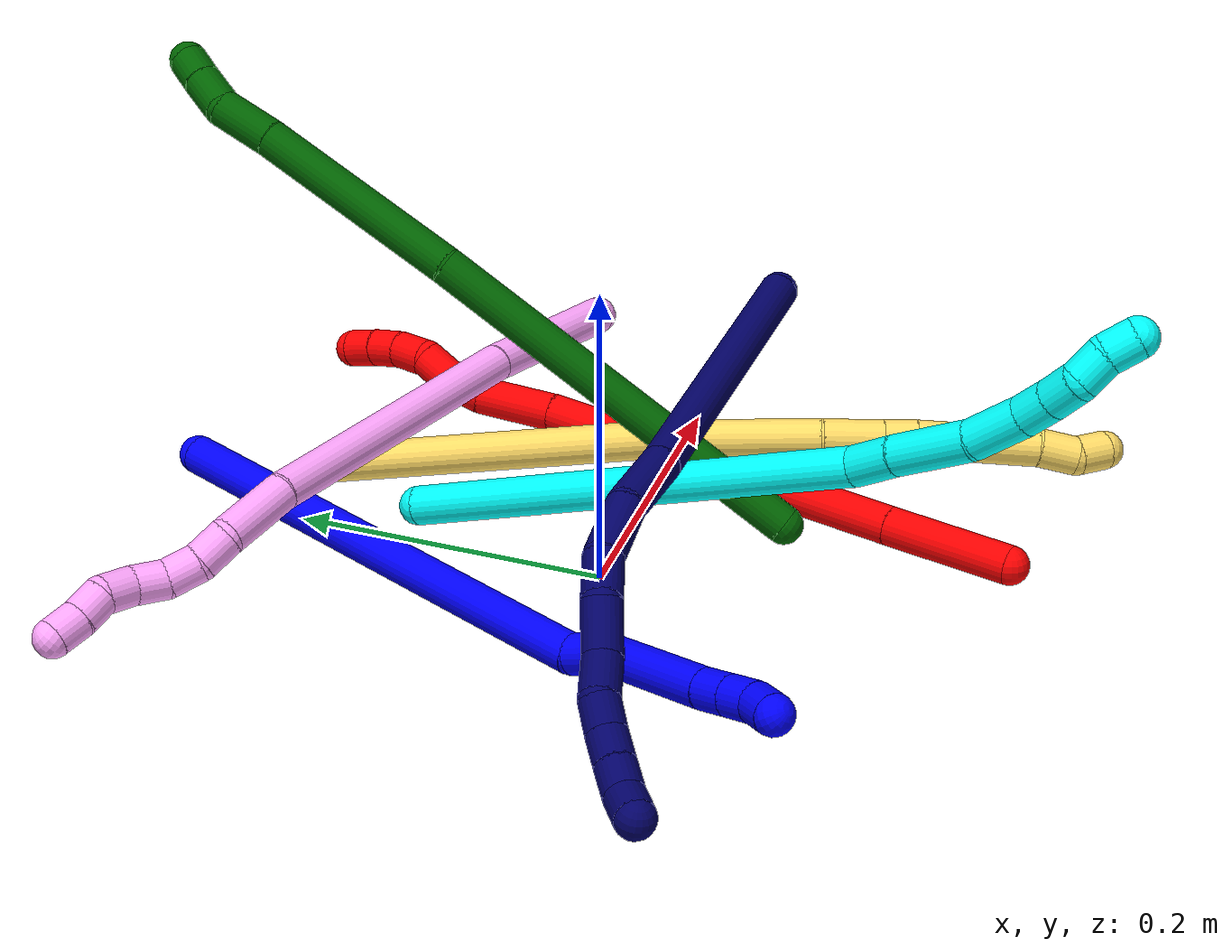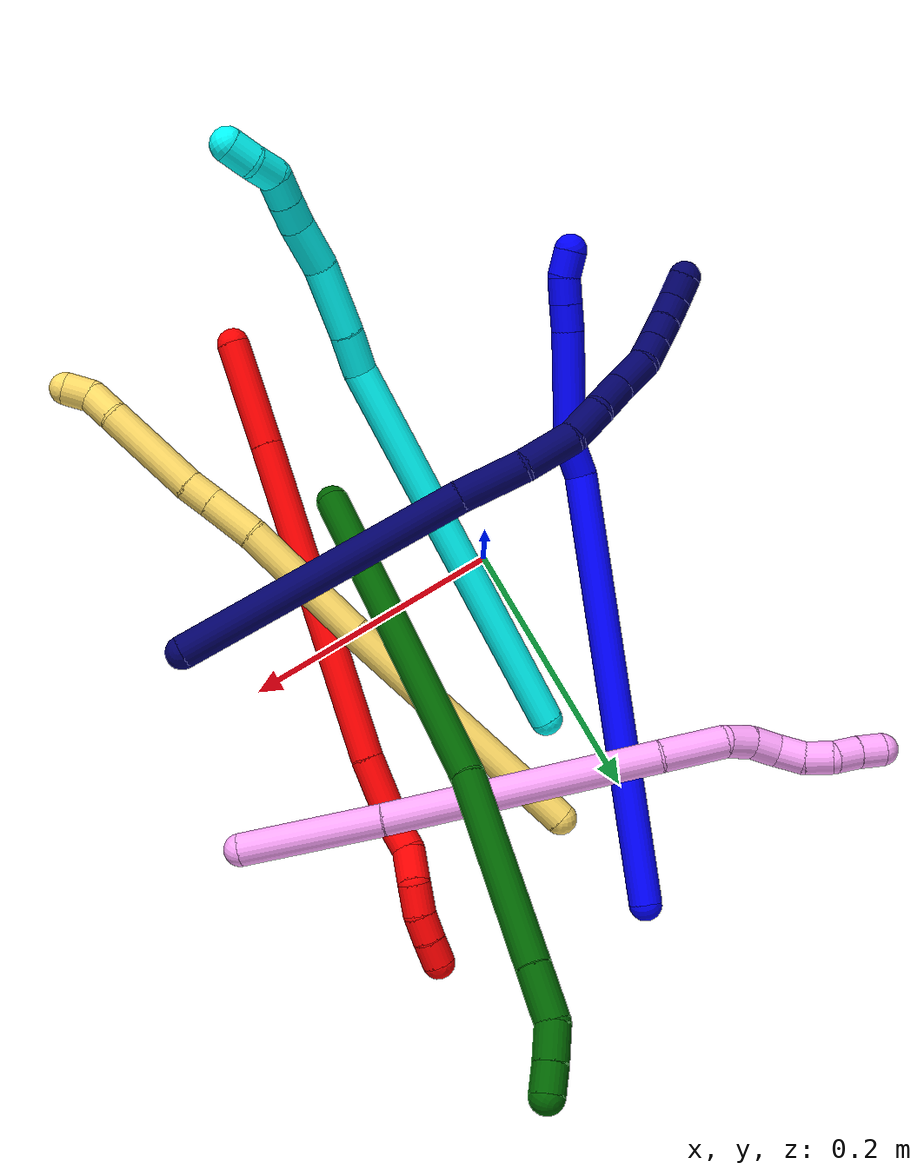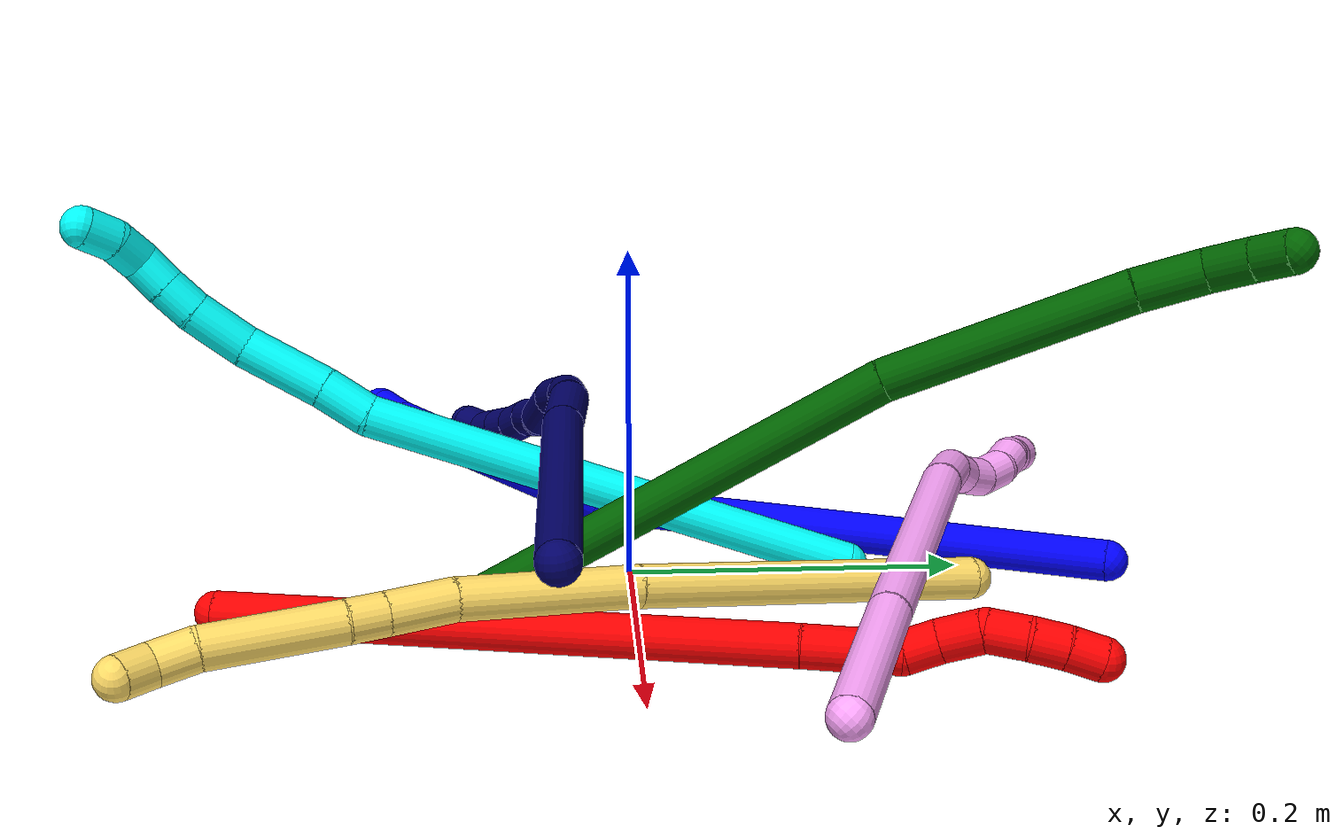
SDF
<sdf version="1.7">
 <world name="default">
  <plugin name="TubeGeneratorPlugin" filename="libtube_generator_plugin.so"/>
  <model name="photoneo_s_sensor">
   <static>1</static>
   <pose>0 0 2 1.57079 1.57079 3.14159</pose>
   <link name="link">
    <inertial><mass>0.1</mass></inertial>
    <sensor name="sensor" type="depth">
     <update_rate>30</update_rate>
     <camera>
      <horizontal_fov>1.22</horizontal_fov>
      <image><width>1920</width><height>1200</height><format>B8G8R8</format></image>
      <clip><near>0.1</near><far>4</far></clip>
      <depth_camera><output>points</output></depth_camera>
     </camera>
     <plugin name="camera_plugin" filename="libgazebo_ros_depth_camera.so">
      <baseline>0.2</baseline>
      <alwaysOn>1</alwaysOn>
      <updateRate>0.0</updateRate>
      <cameraName>camera_ir</cameraName>
      <imageTopicName>/camera/color/image_raw</imageTopicName>
      <cameraInfoTopicName>/camera/color/camera_info</cameraInfoTopicName>
      <depthImageTopicName>/camera/depth/image_raw</depthImageTopicName>
      <depthImageCameraInfoTopicName>/camera/depth/camera_info</depthImageCameraInfoTopicName>
      <pointCloudTopicName>/camera/depth/points</pointCloudTopicName>
      <frameName>fr_optical</frameName>
      <pointCloudCutoff>0.1</pointCloudCutoff>
      <pointCloudCutoffMax>2.0</pointCloudCutoffMax>
      <distortionK1>0</distortionK1>
      <distortionK2>0</distortionK2>
      <distortionK3>0</distortionK3>
      <distortionT1>0</distortionT1>
      <distortionT2>0</distortionT2>
      <CxPrime>0</CxPrime>
      <Cx>0</Cx>
      <Cy>0</Cy>
      <focalLength>0</focalLength>
      <hackBaseline>0</hackBaseline>
     </plugin>
    </sensor>
   </link>
  </model>
  <gravity>0 0 -9.8</gravity>
  <magnetic_field>6e-06 2.3e-05 -4.2e-05</magnetic_field>
  <atmosphere type="adiabatic"/>
  <physics name="default_physics" default="0" type="ode">
   <max_step_size>0.003</max_step_size>
   <real_time_factor>1</real_time_factor>
   <real_time_update_rate>1000</real_time_update_rate>
   <max_contacts>10000</max_contacts>
   <ode>
    <solver>
     <type>quick</type>
     <iters>100</iters>
     <sor>1.3</sor>
     <use_dynamic_moi_rescaling>0</use_dynamic_moi_rescaling>
    </solver>
    <constraints>
     <contact_max_correcting_vel>0</contact_max_correcting_vel>
     <contact_surface_layer>0.001</contact_surface_layer>
     <cfm>0</cfm>
     <erp>0.2</erp>
    </constraints>
   </ode>
  </physics>
  <scene><ambient>0.4 0.4 0.4 1</ambient><background>0.7 0.7 0.7 1</background><shadows>0</shadows></scene>
  <audio><device>default</device></audio>
  <spherical_coordinates>
   <surface_model>EARTH_WGS84</surface_model>
   <latitude_deg>0</latitude_deg>
   <longitude_deg>0</longitude_deg>
   <elevation>0</elevation>
   <heading_deg>0</heading_deg>
  </spherical_coordinates>
  <model name="bin">
   <static>1</static>
   <link name="bottom">
    <collision name="collision-bottom">
     <pose>0 0 -0.01 0 -0 0</pose>
     <geometry><box><size>0.8 0.6 0.02</size></box></geometry>
     <surface>
      <friction><ode><mu>100</mu><mu2>100</mu2></ode></friction>
      <contact><collide_bitmask>65535</collide_bitmask></contact>
     </surface>
    </collision>
   </link>
   <link name="west_wall">
    <collision name="collision-west_wall">
     <pose>-0.41 0 0.1 0 -0 0</pose>
     <geometry><box><size>0.02 0.6 0.2</size></box></geometry>
     <surface>
      <friction><ode><mu>100</mu><mu2>100</mu2></ode></friction>
      <contact><collide_bitmask>65535</collide_bitmask></contact>
     </surface>
    </collision>
   </link>
   <link name="east_wall">
    <collision name="collision-east_wall">
     <pose>0.41 0 0.1 0 -0 0</pose>
     <geometry><box><size>0.02 0.6 0.2</size></box></geometry>
     <surface>
      <friction><ode><mu>100</mu><mu2>100</mu2></ode></friction>
      <contact><collide_bitmask>65535</collide_bitmask></contact>
     </surface>
    </collision>
   </link>
   <link name="south_wall">
    <collision name="collision-south_wall">
     <pose>0 -0.31 0.1 0 -0 0</pose>
     <geometry><box><size>0.8 0.02 0.2</size></box></geometry>
     <surface>
      <friction><ode><mu>100</mu><mu2>100</mu2></ode></friction>
      <contact><collide_bitmask>65535</collide_bitmask></contact>
     </surface>
    </collision>
   </link>
   <link name="north_wall">
    <collision name="collision-north_wall">
     <pose>0 0.31 0.1 0 -0 0</pose>
     <geometry><box><size>0.8 0.02 0.2</size></box></geometry>
     <surface>
      <friction><ode><mu>100</mu><mu2>100</mu2></ode></friction>
      <contact><collide_bitmask>65535</collide_bitmask></contact>
     </surface>
    </collision>
   </link>
  </model>
  <model name="1">
   <static>0</static>
   <link name="1">
    <collision name="collision-cylinder-e_1_1_4">
     <pose>-0.036503 -0.098496 -0.126231 2.47899 -0.224156 -0.632438</pose>
     <geometry><cylinder><radius>0.0125</radius><length>0.328441</length></cylinder></geometry>
     <surface>
      <friction><ode><mu>1.16</mu><mu2>1.16</mu2><slip1>0</slip1><slip2>0</slip2></ode></friction>
      <contact><ode><kp>1e+06</kp><kd>1</kd><max_vel>0</max_vel><min_depth>0.001</min_depth></ode></contact>
     </surface>
    </collision>
    <visual name="visual-cylinder-e_1_1_4">
     <pose>-0.036503 -0.098496 -0.126231 2.47899 -0.224156 -0.632438</pose>
     <geometry><cylinder><radius>0.0125</radius><length>0.328441</length></cylinder></geometry>
     <material><ambient>0 0 1 1</ambient></material>
    </visual>
    <collision name="collision-cylinder-e_2_4_5">
     <pose>-0.075741 -0.199434 -0.264159 2.93578 -0.224935 -1.66019</pose>
     <geometry><cylinder><radius>0.0125</radius><length>0.024514</length></cylinder></geometry>
     <surface>
      <friction><ode><mu>1.16</mu><mu2>1.16</mu2><slip1>0</slip1><slip2>0</slip2></ode></friction>
      <contact><ode><kp>1e+06</kp><kd>1</kd><max_vel>0</max_vel><min_depth>0.001</min_depth></ode></contact>
     </surface>
    </collision>
    <visual name="visual-cylinder-e_2_4_5">
     <pose>-0.075741 -0.199434 -0.264159 2.93578 -0.224935 -1.66019</pose>
     <geometry><cylinder><radius>0.0125</radius><length>0.024514</length></cylinder></geometry>
     <material><ambient>0 0 1 1</ambient></material>
    </visual>
    <collision name="collision-cylinder-e_3_5_6">
     <pose>-0.07882 -0.222502 -0.313796 2.64366 -0.008 -0.031463</pose>
     <geometry><cylinder><radius>0.0125</radius><length>0.086372</length></cylinder></geometry>
     <surface>
      <friction><ode><mu>1.16</mu><mu2>1.16</mu2><slip1>0</slip1><slip2>0</slip2></ode></friction>
      <contact><ode><kp>1e+06</kp><kd>1</kd><max_vel>0</max_vel><min_depth>0.001</min_depth></ode></contact>
     </surface>
    </collision>
    <visual name="visual-cylinder-e_3_5_6">
     <pose>-0.07882 -0.222502 -0.313796 2.64366 -0.008 -0.031463</pose>
     <geometry><cylinder><radius>0.0125</radius><length>0.086372</length></cylinder></geometry>
     <material><ambient>0 0 1 1</ambient></material>
    </visual>
    <collision name="collision-cylinder-e_4_6_7">
     <pose>-0.079598 -0.247492 -0.361065 2.70393 -0.041959 -0.188143</pose>
     <geometry><cylinder><radius>0.0125</radius><length>0.020617</length></cylinder></geometry>
     <surface>
      <friction><ode><mu>1.16</mu><mu2>1.16</mu2><slip1>0</slip1><slip2>0</slip2></ode></friction>
      <contact><ode><kp>1e+06</kp><kd>1</kd><max_vel>0</max_vel><min_depth>0.001</min_depth></ode></contact>
     </surface>
    </collision>
    <visual name="visual-cylinder-e_4_6_7">
     <pose>-0.079598 -0.247492 -0.361065 2.70393 -0.041959 -0.188143</pose>
     <geometry><cylinder><radius>0.0125</radius><length>0.020617</length></cylinder></geometry>
     <material><ambient>0 0 1 1</ambient></material>
    </visual>
    <collision name="collision-cylinder-e_5_7_8">
     <pose>-0.080353 -0.256126 -0.379438 2.70059 -0.032255 -0.14367</pose>
     <geometry><cylinder><radius>0.0125</radius><length>0.020013</length></cylinder></geometry>
     <surface>
      <friction><ode><mu>1.16</mu><mu2>1.16</mu2><slip1>0</slip1><slip2>0</slip2></ode></friction>
      <contact><ode><kp>1e+06</kp><kd>1</kd><max_vel>0</max_vel><min_depth>0.001</min_depth></ode></contact>
     </surface>
    </collision>
    <visual name="visual-cylinder-e_5_7_8">
     <pose>-0.080353 -0.256126 -0.379438 2.70059 -0.032255 -0.14367</pose>
     <geometry><cylinder><radius>0.0125</radius><length>0.020013</length></cylinder></geometry>
     <material><ambient>0 0 1 1</ambient></material>
    </visual>
    <collision name="collision-cylinder-e_6_8_2">
     <pose>-0.078329 -0.265944 -0.396491 2.53572 0.23643 0.726278</pose>
     <geometry><cylinder><radius>0.0125</radius><length>0.020043</length></cylinder></geometry>
     <surface>
      <friction><ode><mu>1.16</mu><mu2>1.16</mu2><slip1>0</slip1><slip2>0</slip2></ode></friction>
      <contact><ode><kp>1e+06</kp><kd>1</kd><max_vel>0</max_vel><min_depth>0.001</min_depth></ode></contact>
     </surface>
    </collision>
    <visual name="visual-cylinder-e_6_8_2">
     <pose>-0.078329 -0.265944 -0.396491 2.53572 0.23643 0.726278</pose>
     <geometry><cylinder><radius>0.0125</radius><length>0.020043</length></cylinder></geometry>
     <material><ambient>0 0 1 1</ambient></material>
    </visual>
    <collision name="collision-sphere-2">
     <pose>-0.075981 -0.271492 -0.4045 0 -0 0</pose>
     <geometry><sphere><radius>0.0125</radius></sphere></geometry>
     <surface>
      <friction><ode><mu>1.16</mu><mu2>1.16</mu2><slip1>0</slip1><slip2>0</slip2></ode></friction>
      <contact><ode><kp>1e+06</kp><kd>1</kd><max_vel>0</max_vel><min_depth>0.001</min_depth></ode></contact>
     </surface>
    </collision>
    <visual name="visual-sphere-2">
     <pose>-0.075981 -0.271492 -0.4045 0 -0 0</pose>
     <geometry><sphere><radius>0.0125</radius></sphere></geometry>
     <material><ambient>0 0 1 1</ambient></material>
    </visual>
    <collision name="collision-sphere-4">
     <pose>-0.073007 -0.196992 -0.252463 0 -0 0</pose>
     <geometry><sphere><radius>0.0125</radius></sphere></geometry>
     <surface>
      <friction><ode><mu>1.16</mu><mu2>1.16</mu2><slip1>0</slip1><slip2>0</slip2></ode></friction>
      <contact><ode><kp>1e+06</kp><kd>1</kd><max_vel>0</max_vel><min_depth>0.001</min_depth></ode></contact>
     </surface>
    </collision>
    <visual name="visual-sphere-4">
     <pose>-0.073007 -0.196992 -0.252463 0 -0 0</pose>
     <geometry><sphere><radius>0.0125</radius></sphere></geometry>
     <material><ambient>0 0 1 1</ambient></material>
    </visual>
    <collision name="collision-sphere-1">
     <geometry><sphere><radius>0.0125</radius></sphere></geometry>
     <surface>
      <friction><ode><mu>1.16</mu><mu2>1.16</mu2><slip1>0</slip1><slip2>0</slip2></ode></friction>
      <contact><ode><kp>1e+06</kp><kd>1</kd><max_vel>0</max_vel><min_depth>0.001</min_depth></ode></contact>
     </surface>
    </collision>
    <visual name="visual-sphere-1">
     <geometry><sphere><radius>0.0125</radius></sphere></geometry>
     <material><ambient>0 0 1 1</ambient></material>
    </visual>
    <collision name="collision-sphere-8">
     <pose>-0.080676 -0.260395 -0.388482 0 -0 0</pose>
     <geometry><sphere><radius>0.0125</radius></sphere></geometry>
     <surface>
      <friction><ode><mu>1.16</mu><mu2>1.16</mu2><slip1>0</slip1><slip2>0</slip2></ode></friction>
      <contact><ode><kp>1e+06</kp><kd>1</kd><max_vel>0</max_vel><min_depth>0.001</min_depth></ode></contact>
     </surface>
    </collision>
    <visual name="visual-sphere-8">
     <pose>-0.080676 -0.260395 -0.388482 0 -0 0</pose>
     <geometry><sphere><radius>0.0125</radius></sphere></geometry>
     <material><ambient>0 0 1 1</ambient></material>
    </visual>
    <collision name="collision-sphere-5">
     <pose>-0.078475 -0.201876 -0.275855 0 -0 0</pose>
     <geometry><sphere><radius>0.0125</radius></sphere></geometry>
     <surface>
      <friction><ode><mu>1.16</mu><mu2>1.16</mu2><slip1>0</slip1><slip2>0</slip2></ode></friction>
      <contact><ode><kp>1e+06</kp><kd>1</kd><max_vel>0</max_vel><min_depth>0.001</min_depth></ode></contact>
     </surface>
    </collision>
    <visual name="visual-sphere-5">
     <pose>-0.078475 -0.201876 -0.275855 0 -0 0</pose>
     <geometry><sphere><radius>0.0125</radius></sphere></geometry>
     <material><ambient>0 0 1 1</ambient></material>
    </visual>
    <collision name="collision-sphere-6">
     <pose>-0.079166 -0.243127 -0.351736 0 -0 0</pose>
     <geometry><sphere><radius>0.0125</radius></sphere></geometry>
     <surface>
      <friction><ode><mu>1.16</mu><mu2>1.16</mu2><slip1>0</slip1><slip2>0</slip2></ode></friction>
      <contact><ode><kp>1e+06</kp><kd>1</kd><max_vel>0</max_vel><min_depth>0.001</min_depth></ode></contact>
     </surface>
    </collision>
    <visual name="visual-sphere-6">
     <pose>-0.079166 -0.243127 -0.351736 0 -0 0</pose>
     <geometry><sphere><radius>0.0125</radius></sphere></geometry>
     <material><ambient>0 0 1 1</ambient></material>
    </visual>
    <collision name="collision-sphere-7">
     <pose>-0.080031 -0.251857 -0.370394 0 -0 0</pose>
     <geometry><sphere><radius>0.0125</radius></sphere></geometry>
     <surface>
      <friction><ode><mu>1.16</mu><mu2>1.16</mu2><slip1>0</slip1><slip2>0</slip2></ode></friction>
      <contact><ode><kp>1e+06</kp><kd>1</kd><max_vel>0</max_vel><min_depth>0.001</min_depth></ode></contact>
     </surface>
    </collision>
    <visual name="visual-sphere-7">
     <pose>-0.080031 -0.251857 -0.370394 0 -0 0</pose>
     <geometry><sphere><radius>0.0125</radius></sphere></geometry>
     <material><ambient>0 0 1 1</ambient></material>
    </visual>
    <inertial>
     <pose>-0.050946 -0.144032 -0.196046 0 -0 0</pose>
     <mass>0.5</mass>
     <inertia>
      <ixx>0.000674</ixx>
      <ixy>0</ixy>
      <ixz>0</ixz>
      <iyy>-0.003433</iyy>
      <iyz>0</iyz>
      <izz>0.002437</izz>
     </inertia>
    </inertial>
   </link>
   <pose>0.02999 0.287514 0.012297 2.34472 -0.460852 2.49894</pose>
  </model>
  <model name="2">
   <static>0</static>
   <link name="2">
    <collision name="collision-cylinder-e_1_1_4">
     <pose>0.009067 0.040051 0.004728 -1.45329 0.22114 -0.196739</pose>
     <geometry><cylinder><radius>0.0125</radius><length>0.082672</length></cylinder></geometry>
     <surface>
      <friction><ode><mu>1.16</mu><mu2>1.16</mu2><slip1>0</slip1><slip2>0</slip2></ode></friction>
      <contact><ode><kp>1e+06</kp><kd>1</kd><max_vel>0</max_vel><min_depth>0.001</min_depth></ode></contact>
     </surface>
    </collision>
    <visual name="visual-cylinder-e_1_1_4">
     <pose>0.009067 0.040051 0.004728 -1.45329 0.22114 -0.196739</pose>
     <geometry><cylinder><radius>0.0125</radius><length>0.082672</length></cylinder></geometry>
     <material><ambient>1 0 0 1</ambient></material>
    </visual>
    <collision name="collision-cylinder-e_2_4_5">
     <pose>0.046518 0.201089 0.024256 -1.44907 0.228798 -0.202706</pose>
     <geometry><cylinder><radius>0.0125</radius><length>0.250301</length></cylinder></geometry>
     <surface>
      <friction><ode><mu>1.16</mu><mu2>1.16</mu2><slip1>0</slip1><slip2>0</slip2></ode></friction>
      <contact><ode><kp>1e+06</kp><kd>1</kd><max_vel>0</max_vel><min_depth>0.001</min_depth></ode></contact>
     </surface>
    </collision>
    <visual name="visual-cylinder-e_2_4_5">
     <pose>0.046518 0.201089 0.024256 -1.44907 0.228798 -0.202706</pose>
     <geometry><cylinder><radius>0.0125</radius><length>0.250301</length></cylinder></geometry>
     <material><ambient>1 0 0 1</ambient></material>
    </visual>
    <collision name="collision-cylinder-e_3_5_6">
     <pose>0.07938 0.349285 0.040847 -1.50508 0.162727 -0.152411</pose>
     <geometry><cylinder><radius>0.0125</radius><length>0.055265</length></cylinder></geometry>
     <surface>
      <friction><ode><mu>1.16</mu><mu2>1.16</mu2><slip1>0</slip1><slip2>0</slip2></ode></friction>
      <contact><ode><kp>1e+06</kp><kd>1</kd><max_vel>0</max_vel><min_depth>0.001</min_depth></ode></contact>
     </surface>
    </collision>
    <visual name="visual-cylinder-e_3_5_6">
     <pose>0.07938 0.349285 0.040847 -1.50508 0.162727 -0.152411</pose>
     <geometry><cylinder><radius>0.0125</radius><length>0.055265</length></cylinder></geometry>
     <material><ambient>1 0 0 1</ambient></material>
    </visual>
    <collision name="collision-cylinder-e_4_6_7">
     <pose>0.083411 0.386434 0.046717 -1.18136 -0.041423 0.027778</pose>
     <geometry><cylinder><radius>0.0125</radius><length>0.021508</length></cylinder></geometry>
     <surface>
      <friction><ode><mu>1.16</mu><mu2>1.16</mu2><slip1>0</slip1><slip2>0</slip2></ode></friction>
      <contact><ode><kp>1e+06</kp><kd>1</kd><max_vel>0</max_vel><min_depth>0.001</min_depth></ode></contact>
     </surface>
    </collision>
    <visual name="visual-cylinder-e_4_6_7">
     <pose>0.083411 0.386434 0.046717 -1.18136 -0.041423 0.027778</pose>
     <geometry><cylinder><radius>0.0125</radius><length>0.021508</length></cylinder></geometry>
     <material><ambient>1 0 0 1</ambient></material>
    </visual>
    <collision name="collision-cylinder-e_5_7_8">
     <pose>0.086671 0.407433 0.056881 -1.06785 0.285488 -0.16953</pose>
     <geometry><cylinder><radius>0.0125</radius><length>0.026309</length></cylinder></geometry>
     <surface>
      <friction><ode><mu>1.16</mu><mu2>1.16</mu2><slip1>0</slip1><slip2>0</slip2></ode></friction>
      <contact><ode><kp>1e+06</kp><kd>1</kd><max_vel>0</max_vel><min_depth>0.001</min_depth></ode></contact>
     </surface>
    </collision>
    <visual name="visual-cylinder-e_5_7_8">
     <pose>0.086671 0.407433 0.056881 -1.06785 0.285488 -0.16953</pose>
     <geometry><cylinder><radius>0.0125</radius><length>0.026309</length></cylinder></geometry>
     <material><ambient>1 0 0 1</ambient></material>
    </visual>
    <collision name="collision-cylinder-e_6_8_9">
     <pose>0.09471 0.429474 0.063514 -1.52083 0.375526 -0.357615</pose>
     <geometry><cylinder><radius>0.0125</radius><length>0.023639</length></cylinder></geometry>
     <surface>
      <friction><ode><mu>1.16</mu><mu2>1.16</mu2><slip1>0</slip1><slip2>0</slip2></ode></friction>
      <contact><ode><kp>1e+06</kp><kd>1</kd><max_vel>0</max_vel><min_depth>0.001</min_depth></ode></contact>
     </surface>
    </collision>
    <visual name="visual-cylinder-e_6_8_9">
     <pose>0.09471 0.429474 0.063514 -1.52083 0.375526 -0.357615</pose>
     <geometry><cylinder><radius>0.0125</radius><length>0.023639</length></cylinder></geometry>
     <material><ambient>1 0 0 1</ambient></material>
    </visual>
    <collision name="collision-cylinder-e_7_9_10">
     <pose>0.101258 0.45027 0.063094 -1.66923 0.220751 -0.24341</pose>
     <geometry><cylinder><radius>0.0125</radius><length>0.020214</length></cylinder></geometry>
     <surface>
      <friction><ode><mu>1.16</mu><mu2>1.16</mu2><slip1>0</slip1><slip2>0</slip2></ode></friction>
      <contact><ode><kp>1e+06</kp><kd>1</kd><max_vel>0</max_vel><min_depth>0.001</min_depth></ode></contact>
     </surface>
    </collision>
    <visual name="visual-cylinder-e_7_9_10">
     <pose>0.101258 0.45027 0.063094 -1.66923 0.220751 -0.24341</pose>
     <geometry><cylinder><radius>0.0125</radius><length>0.020214</length></cylinder></geometry>
     <material><ambient>1 0 0 1</ambient></material>
    </visual>
    <collision name="collision-cylinder-e_8_10_2">
     <pose>0.105482 0.469734 0.060185 -1.76914 0.201485 -0.245602</pose>
     <geometry><cylinder><radius>0.0125</radius><length>0.020093</length></cylinder></geometry>
     <surface>
      <friction><ode><mu>1.16</mu><mu2>1.16</mu2><slip1>0</slip1><slip2>0</slip2></ode></friction>
      <contact><ode><kp>1e+06</kp><kd>1</kd><max_vel>0</max_vel><min_depth>0.001</min_depth></ode></contact>
     </surface>
    </collision>
    <visual name="visual-cylinder-e_8_10_2">
     <pose>0.105482 0.469734 0.060185 -1.76914 0.201485 -0.245602</pose>
     <geometry><cylinder><radius>0.0125</radius><length>0.020093</length></cylinder></geometry>
     <material><ambient>1 0 0 1</ambient></material>
    </visual>
    <collision name="collision-sphere-2">
     <pose>0.107492 0.479385 0.058245 0 -0 0</pose>
     <geometry><sphere><radius>0.0125</radius></sphere></geometry>
     <surface>
      <friction><ode><mu>1.16</mu><mu2>1.16</mu2><slip1>0</slip1><slip2>0</slip2></ode></friction>
      <contact><ode><kp>1e+06</kp><kd>1</kd><max_vel>0</max_vel><min_depth>0.001</min_depth></ode></contact>
     </surface>
    </collision>
    <visual name="visual-sphere-2">
     <pose>0.107492 0.479385 0.058245 0 -0 0</pose>
     <geometry><sphere><radius>0.0125</radius></sphere></geometry>
     <material><ambient>1 0 0 1</ambient></material>
    </visual>
    <collision name="collision-sphere-10">
     <pose>0.103471 0.460084 0.062124 0 -0 0</pose>
     <geometry><sphere><radius>0.0125</radius></sphere></geometry>
     <surface>
      <friction><ode><mu>1.16</mu><mu2>1.16</mu2><slip1>0</slip1><slip2>0</slip2></ode></friction>
      <contact><ode><kp>1e+06</kp><kd>1</kd><max_vel>0</max_vel><min_depth>0.001</min_depth></ode></contact>
     </surface>
    </collision>
    <visual name="visual-sphere-10">
     <pose>0.103471 0.460084 0.062124 0 -0 0</pose>
     <geometry><sphere><radius>0.0125</radius></sphere></geometry>
     <material><ambient>1 0 0 1</ambient></material>
    </visual>
    <collision name="collision-sphere-9">
     <pose>0.099045 0.440456 0.064063 0 -0 0</pose>
     <geometry><sphere><radius>0.0125</radius></sphere></geometry>
     <surface>
      <friction><ode><mu>1.16</mu><mu2>1.16</mu2><slip1>0</slip1><slip2>0</slip2></ode></friction>
      <contact><ode><kp>1e+06</kp><kd>1</kd><max_vel>0</max_vel><min_depth>0.001</min_depth></ode></contact>
     </surface>
    </collision>
    <visual name="visual-sphere-9">
     <pose>0.099045 0.440456 0.064063 0 -0 0</pose>
     <geometry><sphere><radius>0.0125</radius></sphere></geometry>
     <material><ambient>1 0 0 1</ambient></material>
    </visual>
    <collision name="collision-sphere-4">
     <pose>0.018133 0.080102 0.009456 0 -0 0</pose>
     <geometry><sphere><radius>0.0125</radius></sphere></geometry>
     <surface>
      <friction><ode><mu>1.16</mu><mu2>1.16</mu2><slip1>0</slip1><slip2>0</slip2></ode></friction>
      <contact><ode><kp>1e+06</kp><kd>1</kd><max_vel>0</max_vel><min_depth>0.001</min_depth></ode></contact>
     </surface>
    </collision>
    <visual name="visual-sphere-4">
     <pose>0.018133 0.080102 0.009456 0 -0 0</pose>
     <geometry><sphere><radius>0.0125</radius></sphere></geometry>
     <material><ambient>1 0 0 1</ambient></material>
    </visual>
    <collision name="collision-sphere-1">
     <geometry><sphere><radius>0.0125</radius></sphere></geometry>
     <surface>
      <friction><ode><mu>1.16</mu><mu2>1.16</mu2><slip1>0</slip1><slip2>0</slip2></ode></friction>
      <contact><ode><kp>1e+06</kp><kd>1</kd><max_vel>0</max_vel><min_depth>0.001</min_depth></ode></contact>
     </surface>
    </collision>
    <visual name="visual-sphere-1">
     <geometry><sphere><radius>0.0125</radius></sphere></geometry>
     <material><ambient>1 0 0 1</ambient></material>
    </visual>
    <collision name="collision-sphere-8">
     <pose>0.090375 0.418492 0.062965 0 -0 0</pose>
     <geometry><sphere><radius>0.0125</radius></sphere></geometry>
     <surface>
      <friction><ode><mu>1.16</mu><mu2>1.16</mu2><slip1>0</slip1><slip2>0</slip2></ode></friction>
      <contact><ode><kp>1e+06</kp><kd>1</kd><max_vel>0</max_vel><min_depth>0.001</min_depth></ode></contact>
     </surface>
    </collision>
    <visual name="visual-sphere-8">
     <pose>0.090375 0.418492 0.062965 0 -0 0</pose>
     <geometry><sphere><radius>0.0125</radius></sphere></geometry>
     <material><ambient>1 0 0 1</ambient></material>
    </visual>
    <collision name="collision-sphere-5">
     <pose>0.074903 0.322076 0.039057 0 -0 0</pose>
     <geometry><sphere><radius>0.0125</radius></sphere></geometry>
     <surface>
      <friction><ode><mu>1.16</mu><mu2>1.16</mu2><slip1>0</slip1><slip2>0</slip2></ode></friction>
      <contact><ode><kp>1e+06</kp><kd>1</kd><max_vel>0</max_vel><min_depth>0.001</min_depth></ode></contact>
     </surface>
    </collision>
    <visual name="visual-sphere-5">
     <pose>0.074903 0.322076 0.039057 0 -0 0</pose>
     <geometry><sphere><radius>0.0125</radius></sphere></geometry>
     <material><ambient>1 0 0 1</ambient></material>
    </visual>
    <collision name="collision-sphere-6">
     <pose>0.083857 0.376493 0.042638 0 -0 0</pose>
     <geometry><sphere><radius>0.0125</radius></sphere></geometry>
     <surface>
      <friction><ode><mu>1.16</mu><mu2>1.16</mu2><slip1>0</slip1><slip2>0</slip2></ode></friction>
      <contact><ode><kp>1e+06</kp><kd>1</kd><max_vel>0</max_vel><min_depth>0.001</min_depth></ode></contact>
     </surface>
    </collision>
    <visual name="visual-sphere-6">
     <pose>0.083857 0.376493 0.042638 0 -0 0</pose>
     <geometry><sphere><radius>0.0125</radius></sphere></geometry>
     <material><ambient>1 0 0 1</ambient></material>
    </visual>
    <collision name="collision-sphere-7">
     <pose>0.082966 0.396374 0.050797 0 -0 0</pose>
     <geometry><sphere><radius>0.0125</radius></sphere></geometry>
     <surface>
      <friction><ode><mu>1.16</mu><mu2>1.16</mu2><slip1>0</slip1><slip2>0</slip2></ode></friction>
      <contact><ode><kp>1e+06</kp><kd>1</kd><max_vel>0</max_vel><min_depth>0.001</min_depth></ode></contact>
     </surface>
    </collision>
    <visual name="visual-sphere-7">
     <pose>0.082966 0.396374 0.050797 0 -0 0</pose>
     <geometry><sphere><radius>0.0125</radius></sphere></geometry>
     <material><ambient>1 0 0 1</ambient></material>
    </visual>
    <inertial>
     <pose>0.054519 0.24134 0.030414 0 -0 0</pose>
     <mass>0.5</mass>
     <inertia>
      <ixx>0.001065</ixx>
      <ixy>0</ixy>
      <ixz>0</ixz>
      <iyy>-7e-06</iyy>
      <iyz>0</iyz>
      <izz>-0.001656</izz>
     </inertia>
    </inertial>
   </link>
   <pose>0.080801 -0.238747 0.011498 -0.079346 0.14991 0.00954</pose>
  </model>
  <model name="3">
   <static>0</static>
   <link name="3">
    <collision name="collision-cylinder-e_1_1_4">
     <pose>-0.020196 -0.146232 0.024999 1.40148 -0.135301 -0.114183</pose>
     <geometry><cylinder><radius>0.0125</radius><length>0.299443</length></cylinder></geometry>
     <surface>
      <friction><ode><mu>1.16</mu><mu2>1.16</mu2><slip1>0</slip1><slip2>0</slip2></ode></friction>
      <contact><ode><kp>1e+06</kp><kd>1</kd><max_vel>0</max_vel><min_depth>0.001</min_depth></ode></contact>
     </surface>
    </collision>
    <visual name="visual-cylinder-e_1_1_4">
     <pose>-0.020196 -0.146232 0.024999 1.40148 -0.135301 -0.114183</pose>
     <geometry><cylinder><radius>0.0125</radius><length>0.299443</length></cylinder></geometry>
     <material><ambient>0.003922 1 0.996078 1</ambient></material>
    </visual>
    <collision name="collision-cylinder-e_2_4_5">
     <pose>-0.041389 -0.306306 0.05635 1.14056 -0.0654 -0.041954</pose>
     <geometry><cylinder><radius>0.0125</radius><length>0.030526</length></cylinder></geometry>
     <surface>
      <friction><ode><mu>1.16</mu><mu2>1.16</mu2><slip1>0</slip1><slip2>0</slip2></ode></friction>
      <contact><ode><kp>1e+06</kp><kd>1</kd><max_vel>0</max_vel><min_depth>0.001</min_depth></ode></contact>
     </surface>
    </collision>
    <visual name="visual-cylinder-e_2_4_5">
     <pose>-0.041389 -0.306306 0.05635 1.14056 -0.0654 -0.041954</pose>
     <geometry><cylinder><radius>0.0125</radius><length>0.030526</length></cylinder></geometry>
     <material><ambient>0.003922 1 0.996078 1</ambient></material>
    </visual>
    <collision name="collision-cylinder-e_3_5_6">
     <pose>-0.044723 -0.344234 0.071712 1.21283 -0.090607 -0.062867</pose>
     <geometry><cylinder><radius>0.0125</radius><length>0.051643</length></cylinder></geometry>
     <surface>
      <friction><ode><mu>1.16</mu><mu2>1.16</mu2><slip1>0</slip1><slip2>0</slip2></ode></friction>
      <contact><ode><kp>1e+06</kp><kd>1</kd><max_vel>0</max_vel><min_depth>0.001</min_depth></ode></contact>
     </surface>
    </collision>
    <visual name="visual-cylinder-e_3_5_6">
     <pose>-0.044723 -0.344234 0.071712 1.21283 -0.090607 -0.062867</pose>
     <geometry><cylinder><radius>0.0125</radius><length>0.051643</length></cylinder></geometry>
     <material><ambient>0.003922 1 0.996078 1</ambient></material>
    </visual>
    <collision name="collision-cylinder-e_4_6_7">
     <pose>-0.044718 -0.384816 0.087029 1.20561 0.131795 0.090779</pose>
     <geometry><cylinder><radius>0.0125</radius><length>0.035631</length></cylinder></geometry>
     <surface>
      <friction><ode><mu>1.16</mu><mu2>1.16</mu2><slip1>0</slip1><slip2>0</slip2></ode></friction>
      <contact><ode><kp>1e+06</kp><kd>1</kd><max_vel>0</max_vel><min_depth>0.001</min_depth></ode></contact>
     </surface>
    </collision>
    <visual name="visual-cylinder-e_4_6_7">
     <pose>-0.044718 -0.384816 0.087029 1.20561 0.131795 0.090779</pose>
     <geometry><cylinder><radius>0.0125</radius><length>0.035631</length></cylinder></geometry>
     <material><ambient>0.003922 1 0.996078 1</ambient></material>
    </visual>
    <collision name="collision-cylinder-e_5_7_8">
     <pose>-0.04063 -0.410429 0.09825 1.07647 0.167046 0.099882</pose>
     <geometry><cylinder><radius>0.0125</radius><length>0.021005</length></cylinder></geometry>
     <surface>
      <friction><ode><mu>1.16</mu><mu2>1.16</mu2><slip1>0</slip1><slip2>0</slip2></ode></friction>
      <contact><ode><kp>1e+06</kp><kd>1</kd><max_vel>0</max_vel><min_depth>0.001</min_depth></ode></contact>
     </surface>
    </collision>
    <visual name="visual-cylinder-e_5_7_8">
     <pose>-0.04063 -0.410429 0.09825 1.07647 0.167046 0.099882</pose>
     <geometry><cylinder><radius>0.0125</radius><length>0.021005</length></cylinder></geometry>
     <material><ambient>0.003922 1 0.996078 1</ambient></material>
    </visual>
    <collision name="collision-cylinder-e_6_8_9">
     <pose>-0.03691 -0.428319 0.108525 1.02228 0.189667 0.106594</pose>
     <geometry><cylinder><radius>0.0125</radius><length>0.020939</length></cylinder></geometry>
     <surface>
      <friction><ode><mu>1.16</mu><mu2>1.16</mu2><slip1>0</slip1><slip2>0</slip2></ode></friction>
      <contact><ode><kp>1e+06</kp><kd>1</kd><max_vel>0</max_vel><min_depth>0.001</min_depth></ode></contact>
     </surface>
    </collision>
    <visual name="visual-cylinder-e_6_8_9">
     <pose>-0.03691 -0.428319 0.108525 1.02228 0.189667 0.106594</pose>
     <geometry><cylinder><radius>0.0125</radius><length>0.020939</length></cylinder></geometry>
     <material><ambient>0.003922 1 0.996078 1</ambient></material>
    </visual>
    <collision name="collision-cylinder-e_7_9_10">
     <pose>-0.029239 -0.445538 0.115388 1.39474 0.586275 0.495367</pose>
     <geometry><cylinder><radius>0.0125</radius><length>0.020597</length></cylinder></geometry>
     <surface>
      <friction><ode><mu>1.16</mu><mu2>1.16</mu2><slip1>0</slip1><slip2>0</slip2></ode></friction>
      <contact><ode><kp>1e+06</kp><kd>1</kd><max_vel>0</max_vel><min_depth>0.001</min_depth></ode></contact>
     </surface>
    </collision>
    <visual name="visual-cylinder-e_7_9_10">
     <pose>-0.029239 -0.445538 0.115388 1.39474 0.586275 0.495367</pose>
     <geometry><cylinder><radius>0.0125</radius><length>0.020597</length></cylinder></geometry>
     <material><ambient>0.003922 1 0.996078 1</ambient></material>
    </visual>
    <collision name="collision-cylinder-e_8_10_2">
     <pose>-0.020127 -0.463496 0.116663 1.59478 0.344501 0.352692</pose>
     <geometry><cylinder><radius>0.0125</radius><length>0.020216</length></cylinder></geometry>
     <surface>
      <friction><ode><mu>1.16</mu><mu2>1.16</mu2><slip1>0</slip1><slip2>0</slip2></ode></friction>
      <contact><ode><kp>1e+06</kp><kd>1</kd><max_vel>0</max_vel><min_depth>0.001</min_depth></ode></contact>
     </surface>
    </collision>
    <visual name="visual-cylinder-e_8_10_2">
     <pose>-0.020127 -0.463496 0.116663 1.59478 0.344501 0.352692</pose>
     <geometry><cylinder><radius>0.0125</radius><length>0.020216</length></cylinder></geometry>
     <material><ambient>0.003922 1 0.996078 1</ambient></material>
    </visual>
    <collision name="collision-sphere-2">
     <pose>-0.016714 -0.473007 0.116435 0 -0 0</pose>
     <geometry><sphere><radius>0.0125</radius></sphere></geometry>
     <surface>
      <friction><ode><mu>1.16</mu><mu2>1.16</mu2><slip1>0</slip1><slip2>0</slip2></ode></friction>
      <contact><ode><kp>1e+06</kp><kd>1</kd><max_vel>0</max_vel><min_depth>0.001</min_depth></ode></contact>
     </surface>
    </collision>
    <visual name="visual-sphere-2">
     <pose>-0.016714 -0.473007 0.116435 0 -0 0</pose>
     <geometry><sphere><radius>0.0125</radius></sphere></geometry>
     <material><ambient>0.003922 1 0.996078 1</ambient></material>
    </visual>
    <collision name="collision-sphere-10">
     <pose>-0.023541 -0.453984 0.116891 0 -0 0</pose>
     <geometry><sphere><radius>0.0125</radius></sphere></geometry>
     <surface>
      <friction><ode><mu>1.16</mu><mu2>1.16</mu2><slip1>0</slip1><slip2>0</slip2></ode></friction>
      <contact><ode><kp>1e+06</kp><kd>1</kd><max_vel>0</max_vel><min_depth>0.001</min_depth></ode></contact>
     </surface>
    </collision>
    <visual name="visual-sphere-10">
     <pose>-0.023541 -0.453984 0.116891 0 -0 0</pose>
     <geometry><sphere><radius>0.0125</radius></sphere></geometry>
     <material><ambient>0.003922 1 0.996078 1</ambient></material>
    </visual>
    <collision name="collision-sphere-9">
     <pose>-0.034937 -0.437092 0.113886 0 -0 0</pose>
     <geometry><sphere><radius>0.0125</radius></sphere></geometry>
     <surface>
      <friction><ode><mu>1.16</mu><mu2>1.16</mu2><slip1>0</slip1><slip2>0</slip2></ode></friction>
      <contact><ode><kp>1e+06</kp><kd>1</kd><max_vel>0</max_vel><min_depth>0.001</min_depth></ode></contact>
     </surface>
    </collision>
    <visual name="visual-sphere-9">
     <pose>-0.034937 -0.437092 0.113886 0 -0 0</pose>
     <geometry><sphere><radius>0.0125</radius></sphere></geometry>
     <material><ambient>0.003922 1 0.996078 1</ambient></material>
    </visual>
    <collision name="collision-sphere-4">
     <pose>-0.040391 -0.292464 0.049998 0 -0 0</pose>
     <geometry><sphere><radius>0.0125</radius></sphere></geometry>
     <surface>
      <friction><ode><mu>1.16</mu><mu2>1.16</mu2><slip1>0</slip1><slip2>0</slip2></ode></friction>
      <contact><ode><kp>1e+06</kp><kd>1</kd><max_vel>0</max_vel><min_depth>0.001</min_depth></ode></contact>
     </surface>
    </collision>
    <visual name="visual-sphere-4">
     <pose>-0.040391 -0.292464 0.049998 0 -0 0</pose>
     <geometry><sphere><radius>0.0125</radius></sphere></geometry>
     <material><ambient>0.003922 1 0.996078 1</ambient></material>
    </visual>
    <collision name="collision-sphere-1">
     <geometry><sphere><radius>0.0125</radius></sphere></geometry>
     <surface>
      <friction><ode><mu>1.16</mu><mu2>1.16</mu2><slip1>0</slip1><slip2>0</slip2></ode></friction>
      <contact><ode><kp>1e+06</kp><kd>1</kd><max_vel>0</max_vel><min_depth>0.001</min_depth></ode></contact>
     </surface>
    </collision>
    <visual name="visual-sphere-1">
     <geometry><sphere><radius>0.0125</radius></sphere></geometry>
     <material><ambient>0.003922 1 0.996078 1</ambient></material>
    </visual>
    <collision name="collision-sphere-8">
     <pose>-0.038884 -0.419545 0.103163 0 -0 0</pose>
     <geometry><sphere><radius>0.0125</radius></sphere></geometry>
     <surface>
      <friction><ode><mu>1.16</mu><mu2>1.16</mu2><slip1>0</slip1><slip2>0</slip2></ode></friction>
      <contact><ode><kp>1e+06</kp><kd>1</kd><max_vel>0</max_vel><min_depth>0.001</min_depth></ode></contact>
     </surface>
    </collision>
    <visual name="visual-sphere-8">
     <pose>-0.038884 -0.419545 0.103163 0 -0 0</pose>
     <geometry><sphere><radius>0.0125</radius></sphere></geometry>
     <material><ambient>0.003922 1 0.996078 1</ambient></material>
    </visual>
    <collision name="collision-sphere-5">
     <pose>-0.042386 -0.320148 0.062703 0 -0 0</pose>
     <geometry><sphere><radius>0.0125</radius></sphere></geometry>
     <surface>
      <friction><ode><mu>1.16</mu><mu2>1.16</mu2><slip1>0</slip1><slip2>0</slip2></ode></friction>
      <contact><ode><kp>1e+06</kp><kd>1</kd><max_vel>0</max_vel><min_depth>0.001</min_depth></ode></contact>
     </surface>
    </collision>
    <visual name="visual-sphere-5">
     <pose>-0.042386 -0.320148 0.062703 0 -0 0</pose>
     <geometry><sphere><radius>0.0125</radius></sphere></geometry>
     <material><ambient>0.003922 1 0.996078 1</ambient></material>
    </visual>
    <collision name="collision-sphere-6">
     <pose>-0.047059 -0.368319 0.080722 0 -0 0</pose>
     <geometry><sphere><radius>0.0125</radius></sphere></geometry>
     <surface>
      <friction><ode><mu>1.16</mu><mu2>1.16</mu2><slip1>0</slip1><slip2>0</slip2></ode></friction>
      <contact><ode><kp>1e+06</kp><kd>1</kd><max_vel>0</max_vel><min_depth>0.001</min_depth></ode></contact>
     </surface>
    </collision>
    <visual name="visual-sphere-6">
     <pose>-0.047059 -0.368319 0.080722 0 -0 0</pose>
     <geometry><sphere><radius>0.0125</radius></sphere></geometry>
     <material><ambient>0.003922 1 0.996078 1</ambient></material>
    </visual>
    <collision name="collision-sphere-7">
     <pose>-0.042377 -0.401312 0.093337 0 -0 0</pose>
     <geometry><sphere><radius>0.0125</radius></sphere></geometry>
     <surface>
      <friction><ode><mu>1.16</mu><mu2>1.16</mu2><slip1>0</slip1><slip2>0</slip2></ode></friction>
      <contact><ode><kp>1e+06</kp><kd>1</kd><max_vel>0</max_vel><min_depth>0.001</min_depth></ode></contact>
     </surface>
    </collision>
    <visual name="visual-sphere-7">
     <pose>-0.042377 -0.401312 0.093337 0 -0 0</pose>
     <geometry><sphere><radius>0.0125</radius></sphere></geometry>
     <material><ambient>0.003922 1 0.996078 1</ambient></material>
    </visual>
    <inertial>
     <pose>-0.027699 -0.241527 0.050163 0 -0 0</pose>
     <mass>0.5</mass>
     <inertia>
      <ixx>0.001987</ixx>
      <ixy>0</ixy>
      <ixz>0</ixz>
      <iyy>0.000131</iyy>
      <iyz>0</iyz>
      <izz>0.002534</izz>
     </inertia>
    </inertial>
   </link>
   <pose>0.022541 0.129816 0.0115 -0.380838 -0.681251 0.437455</pose>
  </model>
  <model name="4">
   <static>0</static>
   <link name="4">
    <collision name="collision-cylinder-e_1_1_4">
     <pose>-0.042627 0.021876 0.027488 -0.672202 -0.881519 0.326652</pose>
     <geometry><cylinder><radius>0.0125</radius><length>0.110476</length></cylinder></geometry>
     <surface>
      <friction><ode><mu>1.16</mu><mu2>1.16</mu2><slip1>0</slip1><slip2>0</slip2></ode></friction>
      <contact><ode><kp>1e+06</kp><kd>1</kd><max_vel>0</max_vel><min_depth>0.001</min_depth></ode></contact>
     </surface>
    </collision>
    <visual name="visual-cylinder-e_1_1_4">
     <pose>-0.042627 0.021876 0.027488 -0.672202 -0.881519 0.326652</pose>
     <geometry><cylinder><radius>0.0125</radius><length>0.110476</length></cylinder></geometry>
     <material><ambient>1 0.65098 0.996078 1</ambient></material>
    </visual>
    <collision name="collision-cylinder-e_2_4_5">
     <pose>-0.167581 0.091224 0.100679 -0.804381 -0.895785 0.4032</pose>
     <geometry><cylinder><radius>0.0125</radius><length>0.210903</length></cylinder></geometry>
     <surface>
      <friction><ode><mu>1.16</mu><mu2>1.16</mu2><slip1>0</slip1><slip2>0</slip2></ode></friction>
      <contact><ode><kp>1e+06</kp><kd>1</kd><max_vel>0</max_vel><min_depth>0.001</min_depth></ode></contact>
     </surface>
    </collision>
    <visual name="visual-cylinder-e_2_4_5">
     <pose>-0.167581 0.091224 0.100679 -0.804381 -0.895785 0.4032</pose>
     <geometry><cylinder><radius>0.0125</radius><length>0.210903</length></cylinder></geometry>
     <material><ambient>1 0.65098 0.996078 1</ambient></material>
    </visual>
    <collision name="collision-cylinder-e_3_5_6">
     <pose>-0.269038 0.152931 0.154327 -1.06173 -0.865101 0.529401</pose>
     <geometry><cylinder><radius>0.0125</radius><length>0.050268</length></cylinder></geometry>
     <surface>
      <friction><ode><mu>1.16</mu><mu2>1.16</mu2><slip1>0</slip1><slip2>0</slip2></ode></friction>
      <contact><ode><kp>1e+06</kp><kd>1</kd><max_vel>0</max_vel><min_depth>0.001</min_depth></ode></contact>
     </surface>
    </collision>
    <visual name="visual-cylinder-e_3_5_6">
     <pose>-0.269038 0.152931 0.154327 -1.06173 -0.865101 0.529401</pose>
     <geometry><cylinder><radius>0.0125</radius><length>0.050268</length></cylinder></geometry>
     <material><ambient>1 0.65098 0.996078 1</ambient></material>
    </visual>
    <collision name="collision-cylinder-e_4_6_7">
     <pose>-0.293993 0.176746 0.164397 -1.35254 -0.535577 0.433466</pose>
     <geometry><cylinder><radius>0.0125</radius><length>0.022825</length></cylinder></geometry>
     <surface>
      <friction><ode><mu>1.16</mu><mu2>1.16</mu2><slip1>0</slip1><slip2>0</slip2></ode></friction>
      <contact><ode><kp>1e+06</kp><kd>1</kd><max_vel>0</max_vel><min_depth>0.001</min_depth></ode></contact>
     </surface>
    </collision>
    <visual name="visual-cylinder-e_4_6_7">
     <pose>-0.293993 0.176746 0.164397 -1.35254 -0.535577 0.433466</pose>
     <geometry><cylinder><radius>0.0125</radius><length>0.022825</length></cylinder></geometry>
     <material><ambient>1 0.65098 0.996078 1</ambient></material>
    </visual>
    <collision name="collision-cylinder-e_5_7_8">
     <pose>-0.30341 0.195677 0.171094 -1.11592 -0.332378 0.208611</pose>
     <geometry><cylinder><radius>0.0125</radius><length>0.02202</length></cylinder></geometry>
     <surface>
      <friction><ode><mu>1.16</mu><mu2>1.16</mu2><slip1>0</slip1><slip2>0</slip2></ode></friction>
      <contact><ode><kp>1e+06</kp><kd>1</kd><max_vel>0</max_vel><min_depth>0.001</min_depth></ode></contact>
     </surface>
    </collision>
    <visual name="visual-cylinder-e_5_7_8">
     <pose>-0.30341 0.195677 0.171094 -1.11592 -0.332378 0.208611</pose>
     <geometry><cylinder><radius>0.0125</radius><length>0.02202</length></cylinder></geometry>
     <material><ambient>1 0.65098 0.996078 1</ambient></material>
    </visual>
    <collision name="collision-cylinder-e_6_8_9">
     <pose>-0.311276 0.211701 0.183238 -0.722568 -0.400557 0.153115</pose>
     <geometry><cylinder><radius>0.0125</radius><length>0.021922</length></cylinder></geometry>
     <surface>
      <friction><ode><mu>1.16</mu><mu2>1.16</mu2><slip1>0</slip1><slip2>0</slip2></ode></friction>
      <contact><ode><kp>1e+06</kp><kd>1</kd><max_vel>0</max_vel><min_depth>0.001</min_depth></ode></contact>
     </surface>
    </collision>
    <visual name="visual-cylinder-e_6_8_9">
     <pose>-0.311276 0.211701 0.183238 -0.722568 -0.400557 0.153115</pose>
     <geometry><cylinder><radius>0.0125</radius><length>0.021922</length></cylinder></geometry>
     <material><ambient>1 0.65098 0.996078 1</ambient></material>
    </visual>
    <collision name="collision-cylinder-e_7_9_10">
     <pose>-0.322455 0.223357 0.197328 -0.652411 -0.699592 0.245573</pose>
     <geometry><cylinder><radius>0.0125</radius><length>0.021446</length></cylinder></geometry>
     <surface>
      <friction><ode><mu>1.16</mu><mu2>1.16</mu2><slip1>0</slip1><slip2>0</slip2></ode></friction>
      <contact><ode><kp>1e+06</kp><kd>1</kd><max_vel>0</max_vel><min_depth>0.001</min_depth></ode></contact>
     </surface>
    </collision>
    <visual name="visual-cylinder-e_7_9_10">
     <pose>-0.322455 0.223357 0.197328 -0.652411 -0.699592 0.245573</pose>
     <geometry><cylinder><radius>0.0125</radius><length>0.021446</length></cylinder></geometry>
     <material><ambient>1 0.65098 0.996078 1</ambient></material>
    </visual>
    <collision name="collision-cylinder-e_8_10_11">
     <pose>-0.336426 0.235219 0.205804 -1.29377 -0.779292 0.601497</pose>
     <geometry><cylinder><radius>0.0125</radius><length>0.020112</length></cylinder></geometry>
     <surface>
      <friction><ode><mu>1.16</mu><mu2>1.16</mu2><slip1>0</slip1><slip2>0</slip2></ode></friction>
      <contact><ode><kp>1e+06</kp><kd>1</kd><max_vel>0</max_vel><min_depth>0.001</min_depth></ode></contact>
     </surface>
    </collision>
    <visual name="visual-cylinder-e_8_10_11">
     <pose>-0.336426 0.235219 0.205804 -1.29377 -0.779292 0.601497</pose>
     <geometry><cylinder><radius>0.0125</radius><length>0.020112</length></cylinder></geometry>
     <material><ambient>1 0.65098 0.996078 1</ambient></material>
    </visual>
    <collision name="collision-cylinder-e_9_11_2">
     <pose>-0.350247 0.24871 0.211076 -1.10597 -0.740107 0.470018</pose>
     <geometry><cylinder><radius>0.0125</radius><length>0.020029</length></cylinder></geometry>
     <surface>
      <friction><ode><mu>1.16</mu><mu2>1.16</mu2><slip1>0</slip1><slip2>0</slip2></ode></friction>
      <contact><ode><kp>1e+06</kp><kd>1</kd><max_vel>0</max_vel><min_depth>0.001</min_depth></ode></contact>
     </surface>
    </collision>
    <visual name="visual-cylinder-e_9_11_2">
     <pose>-0.350247 0.24871 0.211076 -1.10597 -0.740107 0.470018</pose>
     <geometry><cylinder><radius>0.0125</radius><length>0.020029</length></cylinder></geometry>
     <material><ambient>1 0.65098 0.996078 1</ambient></material>
    </visual>
    <collision name="collision-sphere-2">
     <pose>-0.357 0.25532 0.21439 0 -0 0</pose>
     <geometry><sphere><radius>0.0125</radius></sphere></geometry>
     <surface>
      <friction><ode><mu>1.16</mu><mu2>1.16</mu2><slip1>0</slip1><slip2>0</slip2></ode></friction>
      <contact><ode><kp>1e+06</kp><kd>1</kd><max_vel>0</max_vel><min_depth>0.001</min_depth></ode></contact>
     </surface>
    </collision>
    <visual name="visual-sphere-2">
     <pose>-0.357 0.25532 0.21439 0 -0 0</pose>
     <geometry><sphere><radius>0.0125</radius></sphere></geometry>
     <material><ambient>1 0.65098 0.996078 1</ambient></material>
    </visual>
    <collision name="collision-sphere-11">
     <pose>-0.343493 0.2421 0.207761 0 -0 0</pose>
     <geometry><sphere><radius>0.0125</radius></sphere></geometry>
     <surface>
      <friction><ode><mu>1.16</mu><mu2>1.16</mu2><slip1>0</slip1><slip2>0</slip2></ode></friction>
      <contact><ode><kp>1e+06</kp><kd>1</kd><max_vel>0</max_vel><min_depth>0.001</min_depth></ode></contact>
     </surface>
    </collision>
    <visual name="visual-sphere-11">
     <pose>-0.343493 0.2421 0.207761 0 -0 0</pose>
     <geometry><sphere><radius>0.0125</radius></sphere></geometry>
     <material><ambient>1 0.65098 0.996078 1</ambient></material>
    </visual>
    <collision name="collision-sphere-10">
     <pose>-0.329359 0.228338 0.203848 0 -0 0</pose>
     <geometry><sphere><radius>0.0125</radius></sphere></geometry>
     <surface>
      <friction><ode><mu>1.16</mu><mu2>1.16</mu2><slip1>0</slip1><slip2>0</slip2></ode></friction>
      <contact><ode><kp>1e+06</kp><kd>1</kd><max_vel>0</max_vel><min_depth>0.001</min_depth></ode></contact>
     </surface>
    </collision>
    <visual name="visual-sphere-10">
     <pose>-0.329359 0.228338 0.203848 0 -0 0</pose>
     <geometry><sphere><radius>0.0125</radius></sphere></geometry>
     <material><ambient>1 0.65098 0.996078 1</ambient></material>
    </visual>
    <collision name="collision-sphere-9">
     <pose>-0.31555 0.218376 0.190809 0 -0 0</pose>
     <geometry><sphere><radius>0.0125</radius></sphere></geometry>
     <surface>
      <friction><ode><mu>1.16</mu><mu2>1.16</mu2><slip1>0</slip1><slip2>0</slip2></ode></friction>
      <contact><ode><kp>1e+06</kp><kd>1</kd><max_vel>0</max_vel><min_depth>0.001</min_depth></ode></contact>
     </surface>
    </collision>
    <visual name="visual-sphere-9">
     <pose>-0.31555 0.218376 0.190809 0 -0 0</pose>
     <geometry><sphere><radius>0.0125</radius></sphere></geometry>
     <material><ambient>1 0.65098 0.996078 1</ambient></material>
    </visual>
    <collision name="collision-sphere-4">
     <pose>-0.085255 0.043752 0.054975 0 -0 0</pose>
     <geometry><sphere><radius>0.0125</radius></sphere></geometry>
     <surface>
      <friction><ode><mu>1.16</mu><mu2>1.16</mu2><slip1>0</slip1><slip2>0</slip2></ode></friction>
      <contact><ode><kp>1e+06</kp><kd>1</kd><max_vel>0</max_vel><min_depth>0.001</min_depth></ode></contact>
     </surface>
    </collision>
    <visual name="visual-sphere-4">
     <pose>-0.085255 0.043752 0.054975 0 -0 0</pose>
     <geometry><sphere><radius>0.0125</radius></sphere></geometry>
     <material><ambient>1 0.65098 0.996078 1</ambient></material>
    </visual>
    <collision name="collision-sphere-1">
     <geometry><sphere><radius>0.0125</radius></sphere></geometry>
     <surface>
      <friction><ode><mu>1.16</mu><mu2>1.16</mu2><slip1>0</slip1><slip2>0</slip2></ode></friction>
      <contact><ode><kp>1e+06</kp><kd>1</kd><max_vel>0</max_vel><min_depth>0.001</min_depth></ode></contact>
     </surface>
    </collision>
    <visual name="visual-sphere-1">
     <geometry><sphere><radius>0.0125</radius></sphere></geometry>
     <material><ambient>1 0.65098 0.996078 1</ambient></material>
    </visual>
    <collision name="collision-sphere-8">
     <pose>-0.307002 0.205026 0.175667 0 -0 0</pose>
     <geometry><sphere><radius>0.0125</radius></sphere></geometry>
     <surface>
      <friction><ode><mu>1.16</mu><mu2>1.16</mu2><slip1>0</slip1><slip2>0</slip2></ode></friction>
      <contact><ode><kp>1e+06</kp><kd>1</kd><max_vel>0</max_vel><min_depth>0.001</min_depth></ode></contact>
     </surface>
    </collision>
    <visual name="visual-sphere-8">
     <pose>-0.307002 0.205026 0.175667 0 -0 0</pose>
     <geometry><sphere><radius>0.0125</radius></sphere></geometry>
     <material><ambient>1 0.65098 0.996078 1</ambient></material>
    </visual>
    <collision name="collision-sphere-5">
     <pose>-0.249907 0.138697 0.146383 0 -0 0</pose>
     <geometry><sphere><radius>0.0125</radius></sphere></geometry>
     <surface>
      <friction><ode><mu>1.16</mu><mu2>1.16</mu2><slip1>0</slip1><slip2>0</slip2></ode></friction>
      <contact><ode><kp>1e+06</kp><kd>1</kd><max_vel>0</max_vel><min_depth>0.001</min_depth></ode></contact>
     </surface>
    </collision>
    <visual name="visual-sphere-5">
     <pose>-0.249907 0.138697 0.146383 0 -0 0</pose>
     <geometry><sphere><radius>0.0125</radius></sphere></geometry>
     <material><ambient>1 0.65098 0.996078 1</ambient></material>
    </visual>
    <collision name="collision-sphere-6">
     <pose>-0.288169 0.167165 0.162272 0 -0 0</pose>
     <geometry><sphere><radius>0.0125</radius></sphere></geometry>
     <surface>
      <friction><ode><mu>1.16</mu><mu2>1.16</mu2><slip1>0</slip1><slip2>0</slip2></ode></friction>
      <contact><ode><kp>1e+06</kp><kd>1</kd><max_vel>0</max_vel><min_depth>0.001</min_depth></ode></contact>
     </surface>
    </collision>
    <visual name="visual-sphere-6">
     <pose>-0.288169 0.167165 0.162272 0 -0 0</pose>
     <geometry><sphere><radius>0.0125</radius></sphere></geometry>
     <material><ambient>1 0.65098 0.996078 1</ambient></material>
    </visual>
    <collision name="collision-sphere-7">
     <pose>-0.299817 0.186328 0.166522 0 -0 0</pose>
     <geometry><sphere><radius>0.0125</radius></sphere></geometry>
     <surface>
      <friction><ode><mu>1.16</mu><mu2>1.16</mu2><slip1>0</slip1><slip2>0</slip2></ode></friction>
      <contact><ode><kp>1e+06</kp><kd>1</kd><max_vel>0</max_vel><min_depth>0.001</min_depth></ode></contact>
     </surface>
    </collision>
    <visual name="visual-sphere-7">
     <pose>-0.299817 0.186328 0.166522 0 -0 0</pose>
     <geometry><sphere><radius>0.0125</radius></sphere></geometry>
     <material><ambient>1 0.65098 0.996078 1</ambient></material>
    </visual>
    <inertial>
     <pose>-0.188976 0.11366 0.112327 0 -0 0</pose>
     <mass>0.5</mass>
     <inertia>
      <ixx>0.000735</ixx>
      <ixy>0</ixy>
      <ixz>0</ixz>
      <iyy>0.001043</iyy>
      <iyz>0</iyz>
      <izz>0.000323</izz>
     </inertia>
    </inertial>
   </link>
   <pose>0.26966 0.096458 0.024457 -0.815856 0.075344 0.361078</pose>
  </model>
  <model name="5">
   <static>0</static>
   <link name="5">
    <collision name="collision-cylinder-e_1_1_4">
     <pose>0.040823 -0.093076 0.025674 1.30165 0.400018 0.306327</pose>
     <geometry><cylinder><radius>0.0125</radius><length>0.209655</length></cylinder></geometry>
     <surface>
      <friction><ode><mu>1.16</mu><mu2>1.16</mu2><slip1>0</slip1><slip2>0</slip2></ode></friction>
      <contact><ode><kp>1e+06</kp><kd>1</kd><max_vel>0</max_vel><min_depth>0.001</min_depth></ode></contact>
     </surface>
    </collision>
    <visual name="visual-cylinder-e_1_1_4">
     <pose>0.040823 -0.093076 0.025674 1.30165 0.400018 0.306327</pose>
     <geometry><cylinder><radius>0.0125</radius><length>0.209655</length></cylinder></geometry>
     <material><ambient>1 0.858824 0.4 1</ambient></material>
    </visual>
    <collision name="collision-cylinder-e_2_4_5">
     <pose>0.102952 -0.23331 0.061009 1.36872 0.416665 0.341599</pose>
     <geometry><cylinder><radius>0.0125</radius><length>0.105283</length></cylinder></geometry>
     <surface>
      <friction><ode><mu>1.16</mu><mu2>1.16</mu2><slip1>0</slip1><slip2>0</slip2></ode></friction>
      <contact><ode><kp>1e+06</kp><kd>1</kd><max_vel>0</max_vel><min_depth>0.001</min_depth></ode></contact>
     </surface>
    </collision>
    <visual name="visual-cylinder-e_2_4_5">
     <pose>0.102952 -0.23331 0.061009 1.36872 0.416665 0.341599</pose>
     <geometry><cylinder><radius>0.0125</radius><length>0.105283</length></cylinder></geometry>
     <material><ambient>1 0.858824 0.4 1</ambient></material>
    </visual>
    <collision name="collision-cylinder-e_3_5_6">
     <pose>0.134708 -0.296848 0.073856 1.37869 0.559549 0.465057</pose>
     <geometry><cylinder><radius>0.0125</radius><length>0.03938</length></cylinder></geometry>
     <surface>
      <friction><ode><mu>1.16</mu><mu2>1.16</mu2><slip1>0</slip1><slip2>0</slip2></ode></friction>
      <contact><ode><kp>1e+06</kp><kd>1</kd><max_vel>0</max_vel><min_depth>0.001</min_depth></ode></contact>
     </surface>
    </collision>
    <visual name="visual-cylinder-e_3_5_6">
     <pose>0.134708 -0.296848 0.073856 1.37869 0.559549 0.465057</pose>
     <geometry><cylinder><radius>0.0125</radius><length>0.03938</length></cylinder></geometry>
     <material><ambient>1 0.858824 0.4 1</ambient></material>
    </visual>
    <collision name="collision-cylinder-e_4_6_7">
     <pose>0.150905 -0.322184 0.079008 1.35473 0.559802 0.454409</pose>
     <geometry><cylinder><radius>0.0125</radius><length>0.02164</length></cylinder></geometry>
     <surface>
      <friction><ode><mu>1.16</mu><mu2>1.16</mu2><slip1>0</slip1><slip2>0</slip2></ode></friction>
      <contact><ode><kp>1e+06</kp><kd>1</kd><max_vel>0</max_vel><min_depth>0.001</min_depth></ode></contact>
     </surface>
    </collision>
    <visual name="visual-cylinder-e_4_6_7">
     <pose>0.150905 -0.322184 0.079008 1.35473 0.559802 0.454409</pose>
     <geometry><cylinder><radius>0.0125</radius><length>0.02164</length></cylinder></geometry>
     <material><ambient>1 0.858824 0.4 1</ambient></material>
    </visual>
    <collision name="collision-cylinder-e_5_7_8">
     <pose>0.175336 -0.365234 0.085325 1.44386 0.497939 0.440458</pose>
     <geometry><cylinder><radius>0.0125</radius><length>0.078243</length></cylinder></geometry>
     <surface>
      <friction><ode><mu>1.16</mu><mu2>1.16</mu2><slip1>0</slip1><slip2>0</slip2></ode></friction>
      <contact><ode><kp>1e+06</kp><kd>1</kd><max_vel>0</max_vel><min_depth>0.001</min_depth></ode></contact>
     </surface>
    </collision>
    <visual name="visual-cylinder-e_5_7_8">
     <pose>0.175336 -0.365234 0.085325 1.44386 0.497939 0.440458</pose>
     <geometry><cylinder><radius>0.0125</radius><length>0.078243</length></cylinder></geometry>
     <material><ambient>1 0.858824 0.4 1</ambient></material>
    </visual>
    <collision name="collision-cylinder-e_6_8_9">
     <pose>0.20102 -0.409505 0.089199 1.61766 0.601981 0.629042</pose>
     <geometry><cylinder><radius>0.0125</radius><length>0.024722</length></cylinder></geometry>
     <surface>
      <friction><ode><mu>1.16</mu><mu2>1.16</mu2><slip1>0</slip1><slip2>0</slip2></ode></friction>
      <contact><ode><kp>1e+06</kp><kd>1</kd><max_vel>0</max_vel><min_depth>0.001</min_depth></ode></contact>
     </surface>
    </collision>
    <visual name="visual-cylinder-e_6_8_9">
     <pose>0.20102 -0.409505 0.089199 1.61766 0.601981 0.629042</pose>
     <geometry><cylinder><radius>0.0125</radius><length>0.024722</length></cylinder></geometry>
     <material><ambient>1 0.858824 0.4 1</ambient></material>
    </visual>
    <collision name="collision-cylinder-e_7_9_2">
     <pose>0.21566 -0.425876 0.092505 1.02255 0.81101 0.472696</pose>
     <geometry><cylinder><radius>0.0125</radius><length>0.021077</length></cylinder></geometry>
     <surface>
      <friction><ode><mu>1.16</mu><mu2>1.16</mu2><slip1>0</slip1><slip2>0</slip2></ode></friction>
      <contact><ode><kp>1e+06</kp><kd>1</kd><max_vel>0</max_vel><min_depth>0.001</min_depth></ode></contact>
     </surface>
    </collision>
    <visual name="visual-cylinder-e_7_9_2">
     <pose>0.21566 -0.425876 0.092505 1.02255 0.81101 0.472696</pose>
     <geometry><cylinder><radius>0.0125</radius><length>0.021077</length></cylinder></geometry>
     <material><ambient>1 0.858824 0.4 1</ambient></material>
    </visual>
    <collision name="collision-sphere-2">
     <pose>0.223301 -0.432071 0.096288 0 -0 0</pose>
     <geometry><sphere><radius>0.0125</radius></sphere></geometry>
     <surface>
      <friction><ode><mu>1.16</mu><mu2>1.16</mu2><slip1>0</slip1><slip2>0</slip2></ode></friction>
      <contact><ode><kp>1e+06</kp><kd>1</kd><max_vel>0</max_vel><min_depth>0.001</min_depth></ode></contact>
     </surface>
    </collision>
    <visual name="visual-sphere-2">
     <pose>0.223301 -0.432071 0.096288 0 -0 0</pose>
     <geometry><sphere><radius>0.0125</radius></sphere></geometry>
     <material><ambient>1 0.858824 0.4 1</ambient></material>
    </visual>
    <collision name="collision-sphere-9">
     <pose>0.20802 -0.419681 0.088722 0 -0 0</pose>
     <geometry><sphere><radius>0.0125</radius></sphere></geometry>
     <surface>
      <friction><ode><mu>1.16</mu><mu2>1.16</mu2><slip1>0</slip1><slip2>0</slip2></ode></friction>
      <contact><ode><kp>1e+06</kp><kd>1</kd><max_vel>0</max_vel><min_depth>0.001</min_depth></ode></contact>
     </surface>
    </collision>
    <visual name="visual-sphere-9">
     <pose>0.20802 -0.419681 0.088722 0 -0 0</pose>
     <geometry><sphere><radius>0.0125</radius></sphere></geometry>
     <material><ambient>1 0.858824 0.4 1</ambient></material>
    </visual>
    <collision name="collision-sphere-4">
     <pose>0.081647 -0.186151 0.051347 0 -0 0</pose>
     <geometry><sphere><radius>0.0125</radius></sphere></geometry>
     <surface>
      <friction><ode><mu>1.16</mu><mu2>1.16</mu2><slip1>0</slip1><slip2>0</slip2></ode></friction>
      <contact><ode><kp>1e+06</kp><kd>1</kd><max_vel>0</max_vel><min_depth>0.001</min_depth></ode></contact>
     </surface>
    </collision>
    <visual name="visual-sphere-4">
     <pose>0.081647 -0.186151 0.051347 0 -0 0</pose>
     <geometry><sphere><radius>0.0125</radius></sphere></geometry>
     <material><ambient>1 0.858824 0.4 1</ambient></material>
    </visual>
    <collision name="collision-sphere-1">
     <geometry><sphere><radius>0.0125</radius></sphere></geometry>
     <surface>
      <friction><ode><mu>1.16</mu><mu2>1.16</mu2><slip1>0</slip1><slip2>0</slip2></ode></friction>
      <contact><ode><kp>1e+06</kp><kd>1</kd><max_vel>0</max_vel><min_depth>0.001</min_depth></ode></contact>
     </surface>
    </collision>
    <visual name="visual-sphere-1">
     <geometry><sphere><radius>0.0125</radius></sphere></geometry>
     <material><ambient>1 0.858824 0.4 1</ambient></material>
    </visual>
    <collision name="collision-sphere-8">
     <pose>0.194021 -0.399328 0.089676 0 -0 0</pose>
     <geometry><sphere><radius>0.0125</radius></sphere></geometry>
     <surface>
      <friction><ode><mu>1.16</mu><mu2>1.16</mu2><slip1>0</slip1><slip2>0</slip2></ode></friction>
      <contact><ode><kp>1e+06</kp><kd>1</kd><max_vel>0</max_vel><min_depth>0.001</min_depth></ode></contact>
     </surface>
    </collision>
    <visual name="visual-sphere-8">
     <pose>0.194021 -0.399328 0.089676 0 -0 0</pose>
     <geometry><sphere><radius>0.0125</radius></sphere></geometry>
     <material><ambient>1 0.858824 0.4 1</ambient></material>
    </visual>
    <collision name="collision-sphere-5">
     <pose>0.124256 -0.280468 0.070671 0 -0 0</pose>
     <geometry><sphere><radius>0.0125</radius></sphere></geometry>
     <surface>
      <friction><ode><mu>1.16</mu><mu2>1.16</mu2><slip1>0</slip1><slip2>0</slip2></ode></friction>
      <contact><ode><kp>1e+06</kp><kd>1</kd><max_vel>0</max_vel><min_depth>0.001</min_depth></ode></contact>
     </surface>
    </collision>
    <visual name="visual-sphere-5">
     <pose>0.124256 -0.280468 0.070671 0 -0 0</pose>
     <geometry><sphere><radius>0.0125</radius></sphere></geometry>
     <material><ambient>1 0.858824 0.4 1</ambient></material>
    </visual>
    <collision name="collision-sphere-6">
     <pose>0.145159 -0.313228 0.077042 0 -0 0</pose>
     <geometry><sphere><radius>0.0125</radius></sphere></geometry>
     <surface>
      <friction><ode><mu>1.16</mu><mu2>1.16</mu2><slip1>0</slip1><slip2>0</slip2></ode></friction>
      <contact><ode><kp>1e+06</kp><kd>1</kd><max_vel>0</max_vel><min_depth>0.001</min_depth></ode></contact>
     </surface>
    </collision>
    <visual name="visual-sphere-6">
     <pose>0.145159 -0.313228 0.077042 0 -0 0</pose>
     <geometry><sphere><radius>0.0125</radius></sphere></geometry>
     <material><ambient>1 0.858824 0.4 1</ambient></material>
    </visual>
    <collision name="collision-sphere-7">
     <pose>0.156651 -0.331139 0.080974 0 -0 0</pose>
     <geometry><sphere><radius>0.0125</radius></sphere></geometry>
     <surface>
      <friction><ode><mu>1.16</mu><mu2>1.16</mu2><slip1>0</slip1><slip2>0</slip2></ode></friction>
      <contact><ode><kp>1e+06</kp><kd>1</kd><max_vel>0</max_vel><min_depth>0.001</min_depth></ode></contact>
     </surface>
    </collision>
    <visual name="visual-sphere-7">
     <pose>0.156651 -0.331139 0.080974 0 -0 0</pose>
     <geometry><sphere><radius>0.0125</radius></sphere></geometry>
     <material><ambient>1 0.858824 0.4 1</ambient></material>
    </visual>
    <inertial>
     <pose>0.102404 -0.220832 0.05451 0 -0 0</pose>
     <mass>0.5</mass>
     <inertia>
      <ixx>0.001097</ixx>
      <ixy>0</ixy>
      <ixz>0</ixz>
      <iyy>0.00057</iyy>
      <iyz>0</iyz>
      <izz>0.000464</izz>
     </inertia>
    </inertial>
   </link>
   <pose>0.051826 0.199557 0.011486 -0.185408 0.607354 -0.288963</pose>
  </model>
  <model name="6">
   <static>0</static>
   <link name="6">
    <collision name="collision-cylinder-e_1_1_4">
     <pose>0.027621 0.050304 0.121241 -0.393296 0.207398 -0.041461</pose>
     <geometry><cylinder><radius>0.0125</radius><length>0.268274</length></cylinder></geometry>
     <surface>
      <friction><ode><mu>1.16</mu><mu2>1.16</mu2><slip1>0</slip1><slip2>0</slip2></ode></friction>
      <contact><ode><kp>1e+06</kp><kd>1</kd><max_vel>0</max_vel><min_depth>0.001</min_depth></ode></contact>
     </surface>
    </collision>
    <visual name="visual-cylinder-e_1_1_4">
     <pose>0.027621 0.050304 0.121241 -0.393296 0.207398 -0.041461</pose>
     <geometry><cylinder><radius>0.0125</radius><length>0.268274</length></cylinder></geometry>
     <material><ambient>0 0.392157 0.003922 1</ambient></material>
    </visual>
    <collision name="collision-cylinder-e_2_4_5">
     <pose>0.07468 0.137338 0.3014 -0.557449 0.272984 -0.078569</pose>
     <geometry><cylinder><radius>0.0125</radius><length>0.144197</length></cylinder></geometry>
     <surface>
      <friction><ode><mu>1.16</mu><mu2>1.16</mu2><slip1>0</slip1><slip2>0</slip2></ode></friction>
      <contact><ode><kp>1e+06</kp><kd>1</kd><max_vel>0</max_vel><min_depth>0.001</min_depth></ode></contact>
     </surface>
    </collision>
    <visual name="visual-cylinder-e_2_4_5">
     <pose>0.07468 0.137338 0.3014 -0.557449 0.272984 -0.078569</pose>
     <geometry><cylinder><radius>0.0125</radius><length>0.144197</length></cylinder></geometry>
     <material><ambient>0 0.392157 0.003922 1</ambient></material>
    </visual>
    <collision name="collision-cylinder-e_3_5_6">
     <pose>0.098974 0.185262 0.375696 -0.629211 0.249929 -0.081711</pose>
     <geometry><cylinder><radius>0.0125</radius><length>0.039264</length></cylinder></geometry>
     <surface>
      <friction><ode><mu>1.16</mu><mu2>1.16</mu2><slip1>0</slip1><slip2>0</slip2></ode></friction>
      <contact><ode><kp>1e+06</kp><kd>1</kd><max_vel>0</max_vel><min_depth>0.001</min_depth></ode></contact>
     </surface>
    </collision>
    <visual name="visual-cylinder-e_3_5_6">
     <pose>0.098974 0.185262 0.375696 -0.629211 0.249929 -0.081711</pose>
     <geometry><cylinder><radius>0.0125</radius><length>0.039264</length></cylinder></geometry>
     <material><ambient>0 0.392157 0.003922 1</ambient></material>
    </visual>
    <collision name="collision-cylinder-e_4_6_7">
     <pose>0.11171 0.20378 0.399226 -0.732001 0.623556 -0.245802</pose>
     <geometry><cylinder><radius>0.0125</radius><length>0.026994</length></cylinder></geometry>
     <surface>
      <friction><ode><mu>1.16</mu><mu2>1.16</mu2><slip1>0</slip1><slip2>0</slip2></ode></friction>
      <contact><ode><kp>1e+06</kp><kd>1</kd><max_vel>0</max_vel><min_depth>0.001</min_depth></ode></contact>
     </surface>
    </collision>
    <visual name="visual-cylinder-e_4_6_7">
     <pose>0.11171 0.20378 0.399226 -0.732001 0.623556 -0.245802</pose>
     <geometry><cylinder><radius>0.0125</radius><length>0.026994</length></cylinder></geometry>
     <material><ambient>0 0.392157 0.003922 1</ambient></material>
    </visual>
    <collision name="collision-cylinder-e_5_7_2">
     <pose>0.126204 0.216896 0.413363 -0.768924 0.670889 -0.280251</pose>
     <geometry><cylinder><radius>0.0125</radius><length>0.021271</length></cylinder></geometry>
     <surface>
      <friction><ode><mu>1.16</mu><mu2>1.16</mu2><slip1>0</slip1><slip2>0</slip2></ode></friction>
      <contact><ode><kp>1e+06</kp><kd>1</kd><max_vel>0</max_vel><min_depth>0.001</min_depth></ode></contact>
     </surface>
    </collision>
    <visual name="visual-cylinder-e_5_7_2">
     <pose>0.126204 0.216896 0.413363 -0.768924 0.670889 -0.280251</pose>
     <geometry><cylinder><radius>0.0125</radius><length>0.021271</length></cylinder></geometry>
     <material><ambient>0 0.392157 0.003922 1</ambient></material>
    </visual>
    <collision name="collision-sphere-2">
     <pose>0.132815 0.222688 0.419349 0 -0 0</pose>
     <geometry><sphere><radius>0.0125</radius></sphere></geometry>
     <surface>
      <friction><ode><mu>1.16</mu><mu2>1.16</mu2><slip1>0</slip1><slip2>0</slip2></ode></friction>
      <contact><ode><kp>1e+06</kp><kd>1</kd><max_vel>0</max_vel><min_depth>0.001</min_depth></ode></contact>
     </surface>
    </collision>
    <visual name="visual-sphere-2">
     <pose>0.132815 0.222688 0.419349 0 -0 0</pose>
     <geometry><sphere><radius>0.0125</radius></sphere></geometry>
     <material><ambient>0 0.392157 0.003922 1</ambient></material>
    </visual>
    <collision name="collision-sphere-7">
     <pose>0.119592 0.211103 0.407376 0 -0 0</pose>
     <geometry><sphere><radius>0.0125</radius></sphere></geometry>
     <surface>
      <friction><ode><mu>1.16</mu><mu2>1.16</mu2><slip1>0</slip1><slip2>0</slip2></ode></friction>
      <contact><ode><kp>1e+06</kp><kd>1</kd><max_vel>0</max_vel><min_depth>0.001</min_depth></ode></contact>
     </surface>
    </collision>
    <visual name="visual-sphere-7">
     <pose>0.119592 0.211103 0.407376 0 -0 0</pose>
     <geometry><sphere><radius>0.0125</radius></sphere></geometry>
     <material><ambient>0 0.392157 0.003922 1</ambient></material>
    </visual>
    <collision name="collision-sphere-6">
     <pose>0.103829 0.196457 0.391076 0 -0 0</pose>
     <geometry><sphere><radius>0.0125</radius></sphere></geometry>
     <surface>
      <friction><ode><mu>1.16</mu><mu2>1.16</mu2><slip1>0</slip1><slip2>0</slip2></ode></friction>
      <contact><ode><kp>1e+06</kp><kd>1</kd><max_vel>0</max_vel><min_depth>0.001</min_depth></ode></contact>
     </surface>
    </collision>
    <visual name="visual-sphere-6">
     <pose>0.103829 0.196457 0.391076 0 -0 0</pose>
     <geometry><sphere><radius>0.0125</radius></sphere></geometry>
     <material><ambient>0 0.392157 0.003922 1</ambient></material>
    </visual>
    <collision name="collision-sphere-5">
     <pose>0.094118 0.174068 0.360317 0 -0 0</pose>
     <geometry><sphere><radius>0.0125</radius></sphere></geometry>
     <surface>
      <friction><ode><mu>1.16</mu><mu2>1.16</mu2><slip1>0</slip1><slip2>0</slip2></ode></friction>
      <contact><ode><kp>1e+06</kp><kd>1</kd><max_vel>0</max_vel><min_depth>0.001</min_depth></ode></contact>
     </surface>
    </collision>
    <visual name="visual-sphere-5">
     <pose>0.094118 0.174068 0.360317 0 -0 0</pose>
     <geometry><sphere><radius>0.0125</radius></sphere></geometry>
     <material><ambient>0 0.392157 0.003922 1</ambient></material>
    </visual>
    <collision name="collision-sphere-1">
     <geometry><sphere><radius>0.0125</radius></sphere></geometry>
     <surface>
      <friction><ode><mu>1.16</mu><mu2>1.16</mu2><slip1>0</slip1><slip2>0</slip2></ode></friction>
      <contact><ode><kp>1e+06</kp><kd>1</kd><max_vel>0</max_vel><min_depth>0.001</min_depth></ode></contact>
     </surface>
    </collision>
    <visual name="visual-sphere-1">
     <geometry><sphere><radius>0.0125</radius></sphere></geometry>
     <material><ambient>0 0.392157 0.003922 1</ambient></material>
    </visual>
    <collision name="collision-sphere-4">
     <pose>0.055242 0.100609 0.242482 0 -0 0</pose>
     <geometry><sphere><radius>0.0125</radius></sphere></geometry>
     <surface>
      <friction><ode><mu>1.16</mu><mu2>1.16</mu2><slip1>0</slip1><slip2>0</slip2></ode></friction>
      <contact><ode><kp>1e+06</kp><kd>1</kd><max_vel>0</max_vel><min_depth>0.001</min_depth></ode></contact>
     </surface>
    </collision>
    <visual name="visual-sphere-4">
     <pose>0.055242 0.100609 0.242482 0 -0 0</pose>
     <geometry><sphere><radius>0.0125</radius></sphere></geometry>
     <material><ambient>0 0.392157 0.003922 1</ambient></material>
    </visual>
    <inertial>
     <pose>0.055529 0.101375 0.220614 0 -0 0</pose>
     <mass>0.5</mass>
     <inertia>
      <ixx>0.001762</ixx>
      <ixy>0</ixy>
      <ixz>0</ixz>
      <iyy>0.001659</iyy>
      <iyz>0</iyz>
      <izz>-0.001117</izz>
     </inertia>
    </inertial>
   </link>
   <pose>0.077116 -0.095205 0.012161 -0.693471 -0.404189 -0.064555</pose>
  </model>
  <model name="7">
   <static>0</static>
   <link name="7">
    <collision name="collision-cylinder-e_1_1_4">
     <pose>-0.114625 0.004489 -0.002103 -2.00895 -1.52758 1.96945</pose>
     <geometry><cylinder><radius>0.0125</radius><length>0.229464</length></cylinder></geometry>
     <surface>
      <friction><ode><mu>1.16</mu><mu2>1.16</mu2><slip1>0</slip1><slip2>0</slip2></ode></friction>
      <contact><ode><kp>1e+06</kp><kd>1</kd><max_vel>0</max_vel><min_depth>0.001</min_depth></ode></contact>
     </surface>
    </collision>
    <visual name="visual-cylinder-e_1_1_4">
     <pose>-0.114625 0.004489 -0.002103 -2.00895 -1.52758 1.96945</pose>
     <geometry><cylinder><radius>0.0125</radius><length>0.229464</length></cylinder></geometry>
     <material><ambient>0.003922 0 0.403922 1</ambient></material>
    </visual>
    <collision name="collision-cylinder-e_2_4_5">
     <pose>-0.255031 0.01164 -0.004717 -1.76039 -1.46601 1.65645</pose>
     <geometry><cylinder><radius>0.0125</radius><length>0.051848</length></cylinder></geometry>
     <surface>
      <friction><ode><mu>1.16</mu><mu2>1.16</mu2><slip1>0</slip1><slip2>0</slip2></ode></friction>
      <contact><ode><kp>1e+06</kp><kd>1</kd><max_vel>0</max_vel><min_depth>0.001</min_depth></ode></contact>
     </surface>
    </collision>
    <visual name="visual-cylinder-e_2_4_5">
     <pose>-0.255031 0.01164 -0.004717 -1.76039 -1.46601 1.65645</pose>
     <geometry><cylinder><radius>0.0125</radius><length>0.051848</length></cylinder></geometry>
     <material><ambient>0.003922 0 0.403922 1</ambient></material>
    </visual>
    <collision name="collision-cylinder-e_3_5_6">
     <pose>-0.301822 0.013477 -0.009869 2.96538 -1.35007 -2.92178</pose>
     <geometry><cylinder><radius>0.0125</radius><length>0.043064</length></cylinder></geometry>
     <surface>
      <friction><ode><mu>1.16</mu><mu2>1.16</mu2><slip1>0</slip1><slip2>0</slip2></ode></friction>
      <contact><ode><kp>1e+06</kp><kd>1</kd><max_vel>0</max_vel><min_depth>0.001</min_depth></ode></contact>
     </surface>
    </collision>
    <visual name="visual-cylinder-e_3_5_6">
     <pose>-0.301822 0.013477 -0.009869 2.96538 -1.35007 -2.92178</pose>
     <geometry><cylinder><radius>0.0125</radius><length>0.043064</length></cylinder></geometry>
     <material><ambient>0.003922 0 0.403922 1</ambient></material>
    </visual>
    <collision name="collision-cylinder-e_4_6_7">
     <pose>-0.336463 0.007858 -0.019206 2.34596 -1.11341 -1.95381</pose>
     <geometry><cylinder><radius>0.0125</radius><length>0.030385</length></cylinder></geometry>
     <surface>
      <friction><ode><mu>1.16</mu><mu2>1.16</mu2><slip1>0</slip1><slip2>0</slip2></ode></friction>
      <contact><ode><kp>1e+06</kp><kd>1</kd><max_vel>0</max_vel><min_depth>0.001</min_depth></ode></contact>
     </surface>
    </collision>
    <visual name="visual-cylinder-e_4_6_7">
     <pose>-0.336463 0.007858 -0.019206 2.34596 -1.11341 -1.95381</pose>
     <geometry><cylinder><radius>0.0125</radius><length>0.030385</length></cylinder></geometry>
     <material><ambient>0.003922 0 0.403922 1</ambient></material>
    </visual>
    <collision name="collision-cylinder-e_5_7_8">
     <pose>-0.362384 -0.002837 -0.033956 2.61075 -0.811768 -2.01358</pose>
     <geometry><cylinder><radius>0.0125</radius><length>0.033882</length></cylinder></geometry>
     <surface>
      <friction><ode><mu>1.16</mu><mu2>1.16</mu2><slip1>0</slip1><slip2>0</slip2></ode></friction>
      <contact><ode><kp>1e+06</kp><kd>1</kd><max_vel>0</max_vel><min_depth>0.001</min_depth></ode></contact>
     </surface>
    </collision>
    <visual name="visual-cylinder-e_5_7_8">
     <pose>-0.362384 -0.002837 -0.033956 2.61075 -0.811768 -2.01358</pose>
     <geometry><cylinder><radius>0.0125</radius><length>0.033882</length></cylinder></geometry>
     <material><ambient>0.003922 0 0.403922 1</ambient></material>
    </visual>
    <collision name="collision-cylinder-e_6_8_9">
     <pose>-0.388374 -0.012934 -0.04748 2.26184 -1.19254 -1.92895</pose>
     <geometry><cylinder><radius>0.0125</radius><length>0.029481</length></cylinder></geometry>
     <surface>
      <friction><ode><mu>1.16</mu><mu2>1.16</mu2><slip1>0</slip1><slip2>0</slip2></ode></friction>
      <contact><ode><kp>1e+06</kp><kd>1</kd><max_vel>0</max_vel><min_depth>0.001</min_depth></ode></contact>
     </surface>
    </collision>
    <visual name="visual-cylinder-e_6_8_9">
     <pose>-0.388374 -0.012934 -0.04748 2.26184 -1.19254 -1.92895</pose>
     <geometry><cylinder><radius>0.0125</radius><length>0.029481</length></cylinder></geometry>
     <material><ambient>0.003922 0 0.403922 1</ambient></material>
    </visual>
    <collision name="collision-cylinder-e_7_9_10">
     <pose>-0.40998 -0.022639 -0.055167 2.22418 -0.850544 -1.48439</pose>
     <geometry><cylinder><radius>0.0125</radius><length>0.021042</length></cylinder></geometry>
     <surface>
      <friction><ode><mu>1.16</mu><mu2>1.16</mu2><slip1>0</slip1><slip2>0</slip2></ode></friction>
      <contact><ode><kp>1e+06</kp><kd>1</kd><max_vel>0</max_vel><min_depth>0.001</min_depth></ode></contact>
     </surface>
    </collision>
    <visual name="visual-cylinder-e_7_9_10">
     <pose>-0.40998 -0.022639 -0.055167 2.22418 -0.850544 -1.48439</pose>
     <geometry><cylinder><radius>0.0125</radius><length>0.021042</length></cylinder></geometry>
     <material><ambient>0.003922 0 0.403922 1</ambient></material>
    </visual>
    <collision name="collision-cylinder-e_8_10_11">
     <pose>-0.42598 -0.033761 -0.062028 2.0108 -0.91677 -1.32198</pose>
     <geometry><cylinder><radius>0.0125</radius><length>0.020391</length></cylinder></geometry>
     <surface>
      <friction><ode><mu>1.16</mu><mu2>1.16</mu2><slip1>0</slip1><slip2>0</slip2></ode></friction>
      <contact><ode><kp>1e+06</kp><kd>1</kd><max_vel>0</max_vel><min_depth>0.001</min_depth></ode></contact>
     </surface>
    </collision>
    <visual name="visual-cylinder-e_8_10_11">
     <pose>-0.42598 -0.033761 -0.062028 2.0108 -0.91677 -1.32198</pose>
     <geometry><cylinder><radius>0.0125</radius><length>0.020391</length></cylinder></geometry>
     <material><ambient>0.003922 0 0.403922 1</ambient></material>
    </visual>
    <collision name="collision-cylinder-e_9_11_12">
     <pose>-0.44199 -0.04509 -0.067399 2.01625 -0.896057 -1.30237</pose>
     <geometry><cylinder><radius>0.0125</radius><length>0.020281</length></cylinder></geometry>
     <surface>
      <friction><ode><mu>1.16</mu><mu2>1.16</mu2><slip1>0</slip1><slip2>0</slip2></ode></friction>
      <contact><ode><kp>1e+06</kp><kd>1</kd><max_vel>0</max_vel><min_depth>0.001</min_depth></ode></contact>
     </surface>
    </collision>
    <visual name="visual-cylinder-e_9_11_12">
     <pose>-0.44199 -0.04509 -0.067399 2.01625 -0.896057 -1.30237</pose>
     <geometry><cylinder><radius>0.0125</radius><length>0.020281</length></cylinder></geometry>
     <material><ambient>0.003922 0 0.403922 1</ambient></material>
    </visual>
    <collision name="collision-cylinder-e_10_12_2">
     <pose>-0.458233 -0.056445 -0.069392 1.44086 -0.971491 -0.867946</pose>
     <geometry><cylinder><radius>0.0125</radius><length>0.020162</length></cylinder></geometry>
     <surface>
      <friction><ode><mu>1.16</mu><mu2>1.16</mu2><slip1>0</slip1><slip2>0</slip2></ode></friction>
      <contact><ode><kp>1e+06</kp><kd>1</kd><max_vel>0</max_vel><min_depth>0.001</min_depth></ode></contact>
     </surface>
    </collision>
    <visual name="visual-cylinder-e_10_12_2">
     <pose>-0.458233 -0.056445 -0.069392 1.44086 -0.971491 -0.867946</pose>
     <geometry><cylinder><radius>0.0125</radius><length>0.020162</length></cylinder></geometry>
     <material><ambient>0.003922 0 0.403922 1</ambient></material>
    </visual>
    <collision name="collision-sphere-2">
     <pose>-0.466557 -0.062083 -0.068655 0 -0 0</pose>
     <geometry><sphere><radius>0.0125</radius></sphere></geometry>
     <surface>
      <friction><ode><mu>1.16</mu><mu2>1.16</mu2><slip1>0</slip1><slip2>0</slip2></ode></friction>
      <contact><ode><kp>1e+06</kp><kd>1</kd><max_vel>0</max_vel><min_depth>0.001</min_depth></ode></contact>
     </surface>
    </collision>
    <visual name="visual-sphere-2">
     <pose>-0.466557 -0.062083 -0.068655 0 -0 0</pose>
     <geometry><sphere><radius>0.0125</radius></sphere></geometry>
     <material><ambient>0.003922 0 0.403922 1</ambient></material>
    </visual>
    <collision name="collision-sphere-12">
     <pose>-0.449908 -0.050806 -0.070129 0 -0 0</pose>
     <geometry><sphere><radius>0.0125</radius></sphere></geometry>
     <surface>
      <friction><ode><mu>1.16</mu><mu2>1.16</mu2><slip1>0</slip1><slip2>0</slip2></ode></friction>
      <contact><ode><kp>1e+06</kp><kd>1</kd><max_vel>0</max_vel><min_depth>0.001</min_depth></ode></contact>
     </surface>
    </collision>
    <visual name="visual-sphere-12">
     <pose>-0.449908 -0.050806 -0.070129 0 -0 0</pose>
     <geometry><sphere><radius>0.0125</radius></sphere></geometry>
     <material><ambient>0.003922 0 0.403922 1</ambient></material>
    </visual>
    <collision name="collision-sphere-11">
     <pose>-0.434071 -0.039373 -0.06467 0 -0 0</pose>
     <geometry><sphere><radius>0.0125</radius></sphere></geometry>
     <surface>
      <friction><ode><mu>1.16</mu><mu2>1.16</mu2><slip1>0</slip1><slip2>0</slip2></ode></friction>
      <contact><ode><kp>1e+06</kp><kd>1</kd><max_vel>0</max_vel><min_depth>0.001</min_depth></ode></contact>
     </surface>
    </collision>
    <visual name="visual-sphere-11">
     <pose>-0.434071 -0.039373 -0.06467 0 -0 0</pose>
     <geometry><sphere><radius>0.0125</radius></sphere></geometry>
     <material><ambient>0.003922 0 0.403922 1</ambient></material>
    </visual>
    <collision name="collision-sphere-10">
     <pose>-0.417888 -0.028149 -0.059386 0 -0 0</pose>
     <geometry><sphere><radius>0.0125</radius></sphere></geometry>
     <surface>
      <friction><ode><mu>1.16</mu><mu2>1.16</mu2><slip1>0</slip1><slip2>0</slip2></ode></friction>
      <contact><ode><kp>1e+06</kp><kd>1</kd><max_vel>0</max_vel><min_depth>0.001</min_depth></ode></contact>
     </surface>
    </collision>
    <visual name="visual-sphere-10">
     <pose>-0.417888 -0.028149 -0.059386 0 -0 0</pose>
     <geometry><sphere><radius>0.0125</radius></sphere></geometry>
     <material><ambient>0.003922 0 0.403922 1</ambient></material>
    </visual>
    <collision name="collision-sphere-9">
     <pose>-0.402072 -0.017129 -0.050949 0 -0 0</pose>
     <geometry><sphere><radius>0.0125</radius></sphere></geometry>
     <surface>
      <friction><ode><mu>1.16</mu><mu2>1.16</mu2><slip1>0</slip1><slip2>0</slip2></ode></friction>
      <contact><ode><kp>1e+06</kp><kd>1</kd><max_vel>0</max_vel><min_depth>0.001</min_depth></ode></contact>
     </surface>
    </collision>
    <visual name="visual-sphere-9">
     <pose>-0.402072 -0.017129 -0.050949 0 -0 0</pose>
     <geometry><sphere><radius>0.0125</radius></sphere></geometry>
     <material><ambient>0.003922 0 0.403922 1</ambient></material>
    </visual>
    <collision name="collision-sphere-4">
     <pose>-0.22925 0.008978 -0.004206 0 -0 0</pose>
     <geometry><sphere><radius>0.0125</radius></sphere></geometry>
     <surface>
      <friction><ode><mu>1.16</mu><mu2>1.16</mu2><slip1>0</slip1><slip2>0</slip2></ode></friction>
      <contact><ode><kp>1e+06</kp><kd>1</kd><max_vel>0</max_vel><min_depth>0.001</min_depth></ode></contact>
     </surface>
    </collision>
    <visual name="visual-sphere-4">
     <pose>-0.22925 0.008978 -0.004206 0 -0 0</pose>
     <geometry><sphere><radius>0.0125</radius></sphere></geometry>
     <material><ambient>0.003922 0 0.403922 1</ambient></material>
    </visual>
    <collision name="collision-sphere-1">
     <geometry><sphere><radius>0.0125</radius></sphere></geometry>
     <surface>
      <friction><ode><mu>1.16</mu><mu2>1.16</mu2><slip1>0</slip1><slip2>0</slip2></ode></friction>
      <contact><ode><kp>1e+06</kp><kd>1</kd><max_vel>0</max_vel><min_depth>0.001</min_depth></ode></contact>
     </surface>
    </collision>
    <visual name="visual-sphere-1">
     <geometry><sphere><radius>0.0125</radius></sphere></geometry>
     <material><ambient>0.003922 0 0.403922 1</ambient></material>
    </visual>
    <collision name="collision-sphere-8">
     <pose>-0.374675 -0.008739 -0.04401 0 -0 0</pose>
     <geometry><sphere><radius>0.0125</radius></sphere></geometry>
     <surface>
      <friction><ode><mu>1.16</mu><mu2>1.16</mu2><slip1>0</slip1><slip2>0</slip2></ode></friction>
      <contact><ode><kp>1e+06</kp><kd>1</kd><max_vel>0</max_vel><min_depth>0.001</min_depth></ode></contact>
     </surface>
    </collision>
    <visual name="visual-sphere-8">
     <pose>-0.374675 -0.008739 -0.04401 0 -0 0</pose>
     <geometry><sphere><radius>0.0125</radius></sphere></geometry>
     <material><ambient>0.003922 0 0.403922 1</ambient></material>
    </visual>
    <collision name="collision-sphere-5">
     <pose>-0.280813 0.014303 -0.005228 0 -0 0</pose>
     <geometry><sphere><radius>0.0125</radius></sphere></geometry>
     <surface>
      <friction><ode><mu>1.16</mu><mu2>1.16</mu2><slip1>0</slip1><slip2>0</slip2></ode></friction>
      <contact><ode><kp>1e+06</kp><kd>1</kd><max_vel>0</max_vel><min_depth>0.001</min_depth></ode></contact>
     </surface>
    </collision>
    <visual name="visual-sphere-5">
     <pose>-0.280813 0.014303 -0.005228 0 -0 0</pose>
     <geometry><sphere><radius>0.0125</radius></sphere></geometry>
     <material><ambient>0.003922 0 0.403922 1</ambient></material>
    </visual>
    <collision name="collision-sphere-6">
     <pose>-0.322832 0.012651 -0.014511 0 -0 0</pose>
     <geometry><sphere><radius>0.0125</radius></sphere></geometry>
     <surface>
      <friction><ode><mu>1.16</mu><mu2>1.16</mu2><slip1>0</slip1><slip2>0</slip2></ode></friction>
      <contact><ode><kp>1e+06</kp><kd>1</kd><max_vel>0</max_vel><min_depth>0.001</min_depth></ode></contact>
     </surface>
    </collision>
    <visual name="visual-sphere-6">
     <pose>-0.322832 0.012651 -0.014511 0 -0 0</pose>
     <geometry><sphere><radius>0.0125</radius></sphere></geometry>
     <material><ambient>0.003922 0 0.403922 1</ambient></material>
    </visual>
    <collision name="collision-sphere-7">
     <pose>-0.350093 0.003066 -0.023901 0 -0 0</pose>
     <geometry><sphere><radius>0.0125</radius></sphere></geometry>
     <surface>
      <friction><ode><mu>1.16</mu><mu2>1.16</mu2><slip1>0</slip1><slip2>0</slip2></ode></friction>
      <contact><ode><kp>1e+06</kp><kd>1</kd><max_vel>0</max_vel><min_depth>0.001</min_depth></ode></contact>
     </surface>
    </collision>
    <visual name="visual-sphere-7">
     <pose>-0.350093 0.003066 -0.023901 0 -0 0</pose>
     <geometry><sphere><radius>0.0125</radius></sphere></geometry>
     <material><ambient>0.003922 0 0.403922 1</ambient></material>
    </visual>
    <inertial>
     <pose>-0.24398 -0.002484 -0.018955 0 -0 0</pose>
     <mass>0.5</mass>
     <inertia>
      <ixx>-2.4e-05</ixx>
      <ixy>0</ixy>
      <ixz>0</ixz>
      <iyy>0.001077</iyy>
      <iyz>0</iyz>
      <izz>0.001012</izz>
     </inertia>
    </inertial>
   </link>
   <pose>0.226479 -0.045318 0.092434 0.149244 0.018495 0.016733</pose>
  </model>
 </world>
</sdf>
